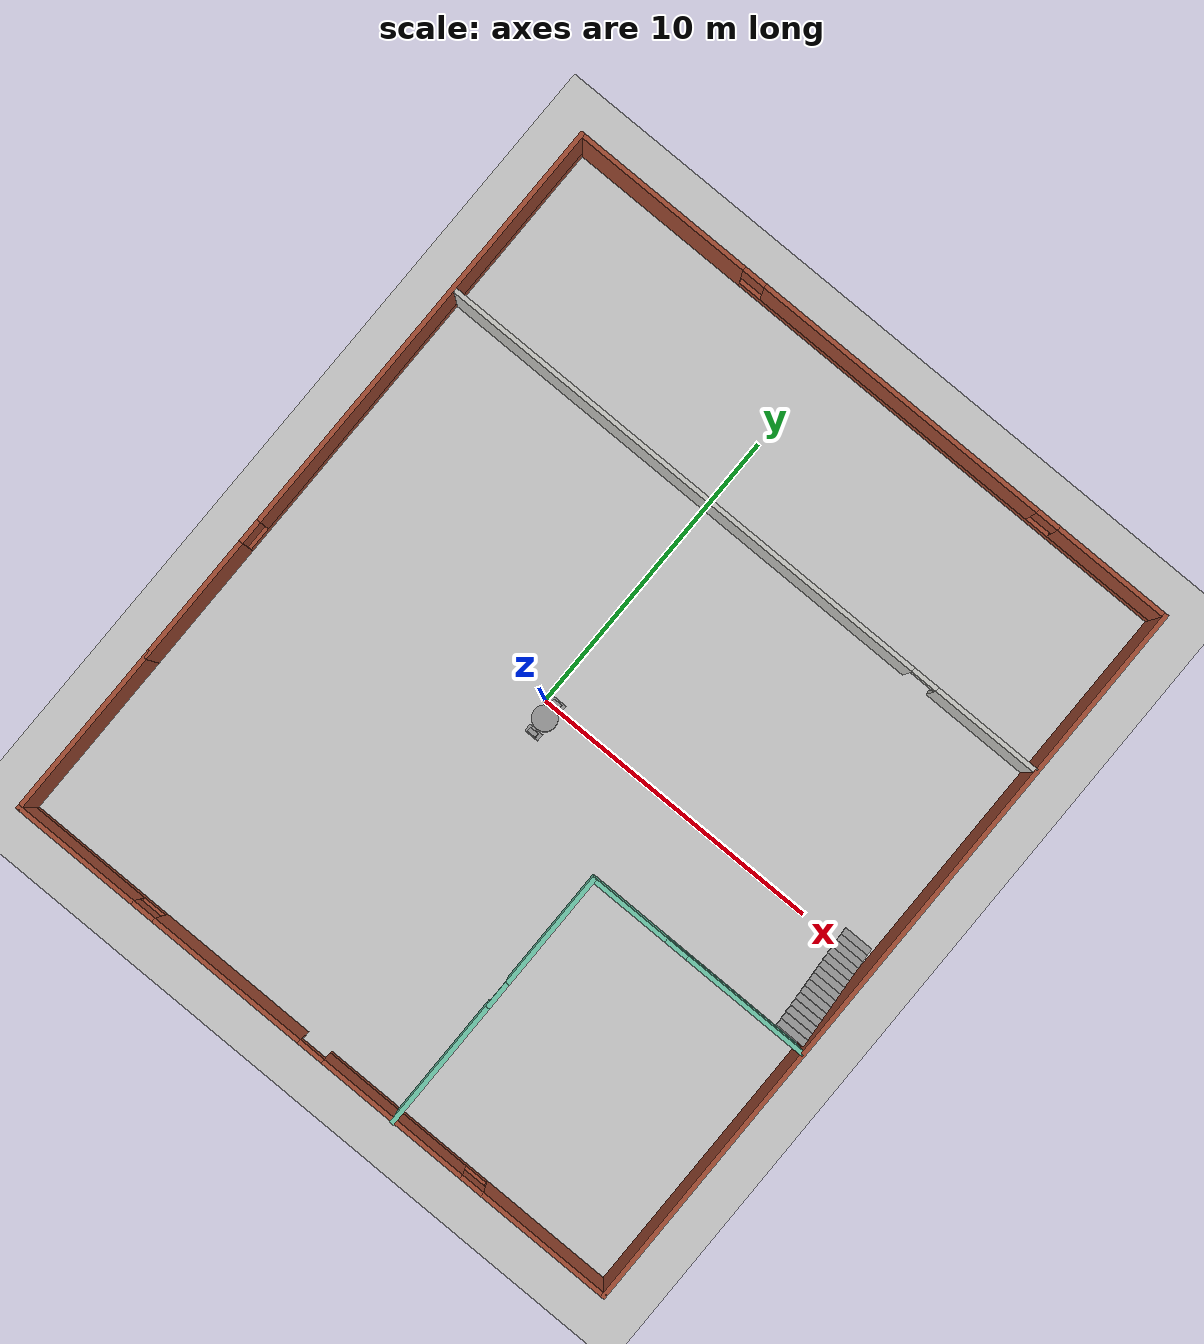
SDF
<sdf version="1.6">
 <world name="default">
  <plugin name="hello" filename="libhello.so"/>
  <light name="sun" type="directional">
   <pose>0 0 10 0 -0 0</pose>
   <diffuse>0.8 0.8 0.8 1</diffuse>
   <specular>0.2 0.2 0.2 1</specular>
   <attenuation>
    <range>1000</range>
    <constant>0.9</constant>
    <linear>0.01</linear>
    <quadratic>0.001</quadratic>
   </attenuation>
   <direction>-0.5 0.1 -0.9</direction>
  </light>
  <model name="ground_plane">
   <static>1</static>
   <link name="link">
    <collision name="collision">
     <geometry><plane><normal>0 0 1</normal><size>100 100</size></plane></geometry>
     <surface>
      <contact><collide_bitmask>65535</collide_bitmask></contact>
      <friction><ode><mu>100</mu><mu2>50</mu2></ode></friction>
     </surface>
    </collision>
    <visual name="visual">
     <cast_shadows>0</cast_shadows>
     <geometry><plane><normal>0 0 1</normal><size>100 100</size></plane></geometry>
     <material>
      <script><uri>file://media/materials/scripts/gazebo.material</uri><name>Gazebo/Grey</name></script>
     </material>
    </visual>
   </link>
  </model>
  <gravity>0 0 -9.8</gravity>
  <magnetic_field>6e-06 2.3e-05 -4.2e-05</magnetic_field>
  <atmosphere type="adiabatic"/>
  <physics name="default_physics" default="0" type="ode">
   <max_step_size>0.001</max_step_size>
   <real_time_factor>1</real_time_factor>
   <real_time_update_rate>1000</real_time_update_rate>
  </physics>
  <scene><ambient>0.4 0.4 0.4 1</ambient><background>0.7 0.7 0.7 1</background><shadows>1</shadows></scene>
  <spherical_coordinates>
   <surface_model>EARTH_WGS84</surface_model>
   <latitude_deg>0</latitude_deg>
   <longitude_deg>0</longitude_deg>
   <elevation>0</elevation>
   <heading_deg>0</heading_deg>
  </spherical_coordinates>
  <model name="robot3">
   <link name="link_2">
    <pose>0.005 -0 -0.064976 0 -0 0</pose>
    <inertial>
     <mass>1</mass>
     <inertia><ixx>0.145833</ixx><ixy>0</ixy><ixz>0</ixz><iyy>0.145833</iyy><iyz>0</iyz><izz>0.125</izz></inertia>
    </inertial>
    <visual name="visual">
     <geometry><cylinder><radius>0.4</radius><length>0.8</length></cylinder></geometry>
     <material>
      <lighting>1</lighting>
      <script><uri>file://media/materials/scripts/gazebo.material</uri><name>Gazebo/Grey</name></script>
      <shader type="pixel"><normal_map>__default__</normal_map></shader>
      <ambient>0.3 0.3 0.3 1</ambient>
      <diffuse>0.7 0.7 0.7 1</diffuse>
      <specular>0.01 0.01 0.01 1</specular>
      <emissive>0 0 0 1</emissive>
     </material>
    </visual>
    <collision name="collision">
     <geometry><cylinder><radius>0.4</radius><length>0.8</length></cylinder></geometry>
     <surface>
      <friction>
       <ode><mu>1</mu><mu2>1</mu2><fdir1>0 0 0</fdir1><slip1>0</slip1><slip2>0</slip2></ode>
       <torsional>
        <coefficient>1</coefficient>
        <patch_radius>0</patch_radius>
        <surface_radius>0</surface_radius>
        <use_patch_radius>1</use_patch_radius>
        <ode><slip>0</slip></ode>
       </torsional>
      </friction>
      <bounce><restitution_coefficient>0</restitution_coefficient><threshold>1e+06</threshold></bounce>
      <contact>
       <collide_without_contact>0</collide_without_contact>
       <collide_without_contact_bitmask>1</collide_without_contact_bitmask>
       <collide_bitmask>1</collide_bitmask>
       <ode>
        <soft_cfm>0</soft_cfm>
        <soft_erp>0.2</soft_erp>
        <kp>1e+13</kp>
        <kd>1</kd>
        <max_vel>0.01</max_vel>
        <min_depth>0</min_depth>
       </ode>
       <bullet>
        <split_impulse>1</split_impulse>
        <split_impulse_penetration_threshold>-0.01</split_impulse_penetration_threshold>
        <soft_cfm>0</soft_cfm>
        <soft_erp>0.2</soft_erp>
        <kp>1e+13</kp>
        <kd>1</kd>
       </bullet>
      </contact>
     </surface>
    </collision>
   </link>
   <link name="link_0">
    <pose>0.00499 0.565134 -0.515032 -0.000625 0 -0.000608</pose>
    <inertial>
     <mass>1</mass>
     <inertia>
      <ixx>0.166667</ixx>
      <ixy>0</ixy>
      <ixz>0</ixz>
      <iyy>0.166667</iyy>
      <iyz>0</iyz>
      <izz>0.166667</izz>
     </inertia>
    </inertial>
    <visual name="visual">
     <geometry><box><size>0.5 0.25 0.1</size></box></geometry>
     <material>
      <lighting>1</lighting>
      <script><uri>file://media/materials/scripts/gazebo.material</uri><name>Gazebo/Grey</name></script>
      <shader type="pixel"><normal_map>__default__</normal_map></shader>
      <ambient>0.3 0.3 0.3 1</ambient>
      <diffuse>0.7 0.7 0.7 1</diffuse>
      <specular>0.01 0.01 0.01 1</specular>
      <emissive>0 0 0 1</emissive>
     </material>
    </visual>
    <collision name="collision">
     <geometry><box><size>0.5 0.25 0.1</size></box></geometry>
     <surface>
      <friction>
       <ode><mu>1</mu><mu2>1</mu2><fdir1>0 0 0</fdir1><slip1>0</slip1><slip2>0</slip2></ode>
       <torsional>
        <coefficient>1</coefficient>
        <patch_radius>0</patch_radius>
        <surface_radius>0</surface_radius>
        <use_patch_radius>1</use_patch_radius>
        <ode><slip>0</slip></ode>
       </torsional>
      </friction>
      <bounce><restitution_coefficient>0</restitution_coefficient><threshold>1e+06</threshold></bounce>
      <contact>
       <collide_without_contact>0</collide_without_contact>
       <collide_without_contact_bitmask>1</collide_without_contact_bitmask>
       <collide_bitmask>1</collide_bitmask>
       <ode>
        <soft_cfm>0</soft_cfm>
        <soft_erp>0.2</soft_erp>
        <kp>1e+13</kp>
        <kd>1</kd>
        <max_vel>0.01</max_vel>
        <min_depth>0</min_depth>
       </ode>
       <bullet>
        <split_impulse>1</split_impulse>
        <split_impulse_penetration_threshold>-0.01</split_impulse_penetration_threshold>
        <soft_cfm>0</soft_cfm>
        <soft_erp>0.2</soft_erp>
        <kp>1e+13</kp>
        <kd>1</kd>
       </bullet>
      </contact>
     </surface>
    </collision>
   </link>
   <link name="link_0_clone">
    <pose>0.00499 -0.535072 -0.514954 -0.00125 -1e-06 -0.001216</pose>
    <inertial>
     <mass>1</mass>
     <inertia>
      <ixx>0.166667</ixx>
      <ixy>0</ixy>
      <ixz>0</ixz>
      <iyy>0.166667</iyy>
      <iyz>0</iyz>
      <izz>0.166667</izz>
     </inertia>
    </inertial>
    <visual name="visual">
     <geometry><box><size>0.5 0.25 0.1</size></box></geometry>
     <material>
      <lighting>1</lighting>
      <script><uri>file://media/materials/scripts/gazebo.material</uri><name>Gazebo/Grey</name></script>
      <shader type="pixel"><normal_map>__default__</normal_map></shader>
      <ambient>0.3 0.3 0.3 1</ambient>
      <diffuse>0.7 0.7 0.7 1</diffuse>
      <specular>0.01 0.01 0.01 1</specular>
      <emissive>0 0 0 1</emissive>
     </material>
    </visual>
    <collision name="collision">
     <geometry><box><size>0.5 0.25 0.1</size></box></geometry>
     <surface>
      <friction>
       <ode><mu>1</mu><mu2>1</mu2><fdir1>0 0 0</fdir1><slip1>0</slip1><slip2>0</slip2></ode>
       <torsional>
        <coefficient>1</coefficient>
        <patch_radius>0</patch_radius>
        <surface_radius>0</surface_radius>
        <use_patch_radius>1</use_patch_radius>
        <ode><slip>0</slip></ode>
       </torsional>
      </friction>
      <bounce><restitution_coefficient>0</restitution_coefficient><threshold>1e+06</threshold></bounce>
      <contact>
       <collide_without_contact>0</collide_without_contact>
       <collide_without_contact_bitmask>1</collide_without_contact_bitmask>
       <collide_bitmask>1</collide_bitmask>
       <ode>
        <soft_cfm>0</soft_cfm>
        <soft_erp>0.2</soft_erp>
        <kp>1e+13</kp>
        <kd>1</kd>
        <max_vel>0.01</max_vel>
        <min_depth>0</min_depth>
       </ode>
       <bullet>
        <split_impulse>1</split_impulse>
        <split_impulse_penetration_threshold>-0.01</split_impulse_penetration_threshold>
        <soft_cfm>0</soft_cfm>
        <soft_erp>0.2</soft_erp>
        <kp>1e+13</kp>
        <kd>1</kd>
       </bullet>
      </contact>
     </surface>
    </collision>
   </link>
   <link name="link_3">
    <pose>-0.015 -1e-06 0.194928 1.5707 -0 0</pose>
    <inertial>
     <mass>1</mass>
     <inertia><ixx>0.145833</ixx><ixy>0</ixy><ixz>0</ixz><iyy>0.145833</iyy><iyz>0</iyz><izz>0.125</izz></inertia>
    </inertial>
    <visual name="visual">
     <geometry><cylinder><radius>0.1</radius><length>1.25</length></cylinder></geometry>
     <material>
      <lighting>1</lighting>
      <script><uri>file://media/materials/scripts/gazebo.material</uri><name>Gazebo/Grey</name></script>
      <shader type="pixel"><normal_map>__default__</normal_map></shader>
      <ambient>0.3 0.3 0.3 1</ambient>
      <diffuse>0.7 0.7 0.7 1</diffuse>
      <specular>0.01 0.01 0.01 1</specular>
      <emissive>0 0 0 1</emissive>
     </material>
    </visual>
    <collision name="collision">
     <geometry><cylinder><radius>0.1</radius><length>1.25</length></cylinder></geometry>
     <surface>
      <friction>
       <ode><mu>1</mu><mu2>1</mu2><fdir1>0 0 0</fdir1><slip1>0</slip1><slip2>0</slip2></ode>
       <torsional>
        <coefficient>1</coefficient>
        <patch_radius>0</patch_radius>
        <surface_radius>0</surface_radius>
        <use_patch_radius>1</use_patch_radius>
        <ode><slip>0</slip></ode>
       </torsional>
      </friction>
      <bounce><restitution_coefficient>0</restitution_coefficient><threshold>1e+06</threshold></bounce>
      <contact>
       <collide_without_contact>0</collide_without_contact>
       <collide_without_contact_bitmask>1</collide_without_contact_bitmask>
       <collide_bitmask>1</collide_bitmask>
       <ode>
        <soft_cfm>0</soft_cfm>
        <soft_erp>0.2</soft_erp>
        <kp>1e+13</kp>
        <kd>1</kd>
        <max_vel>0.01</max_vel>
        <min_depth>0</min_depth>
       </ode>
       <bullet>
        <split_impulse>1</split_impulse>
        <split_impulse_penetration_threshold>-0.01</split_impulse_penetration_threshold>
        <soft_cfm>0</soft_cfm>
        <soft_erp>0.2</soft_erp>
        <kp>1e+13</kp>
        <kd>1</kd>
       </bullet>
      </contact>
     </surface>
    </collision>
   </link>
   <link name="link_4">
    <pose>0.005 -0.550011 -0.064976 0 -0 0</pose>
    <inertial>
     <mass>1</mass>
     <inertia>
      <ixx>0.166667</ixx>
      <ixy>0</ixy>
      <ixz>0</ixz>
      <iyy>0.166667</iyy>
      <iyz>0</iyz>
      <izz>0.166667</izz>
     </inertia>
    </inertial>
    <visual name="visual">
     <geometry><box><size>0.3 0.15 1</size></box></geometry>
     <material>
      <lighting>1</lighting>
      <script><uri>file://media/materials/scripts/gazebo.material</uri><name>Gazebo/Grey</name></script>
      <shader type="pixel"><normal_map>__default__</normal_map></shader>
      <ambient>0.3 0.3 0.3 1</ambient>
      <diffuse>0.7 0.7 0.7 1</diffuse>
      <specular>0.01 0.01 0.01 1</specular>
      <emissive>0 0 0 1</emissive>
     </material>
    </visual>
    <collision name="collision">
     <geometry><box><size>0.3 0.15 1</size></box></geometry>
     <surface>
      <friction>
       <ode><mu>1</mu><mu2>1</mu2><fdir1>0 0 0</fdir1><slip1>0</slip1><slip2>0</slip2></ode>
       <torsional>
        <coefficient>1</coefficient>
        <patch_radius>0</patch_radius>
        <surface_radius>0</surface_radius>
        <use_patch_radius>1</use_patch_radius>
        <ode><slip>0</slip></ode>
       </torsional>
      </friction>
      <bounce><restitution_coefficient>0</restitution_coefficient><threshold>1e+06</threshold></bounce>
      <contact>
       <collide_without_contact>0</collide_without_contact>
       <collide_without_contact_bitmask>1</collide_without_contact_bitmask>
       <collide_bitmask>1</collide_bitmask>
       <ode>
        <soft_cfm>0</soft_cfm>
        <soft_erp>0.2</soft_erp>
        <kp>1e+13</kp>
        <kd>1</kd>
        <max_vel>0.01</max_vel>
        <min_depth>0</min_depth>
       </ode>
       <bullet>
        <split_impulse>1</split_impulse>
        <split_impulse_penetration_threshold>-0.01</split_impulse_penetration_threshold>
        <soft_cfm>0</soft_cfm>
        <soft_erp>0.2</soft_erp>
        <kp>1e+13</kp>
        <kd>1</kd>
       </bullet>
      </contact>
     </surface>
    </collision>
   </link>
   <link name="link_4_clone">
    <pose>0.005 0.550012 -0.064976 0 -0 0</pose>
    <inertial>
     <mass>1</mass>
     <inertia>
      <ixx>0.166667</ixx>
      <ixy>0</ixy>
      <ixz>0</ixz>
      <iyy>0.166667</iyy>
      <iyz>0</iyz>
      <izz>0.166667</izz>
     </inertia>
    </inertial>
    <visual name="visual">
     <geometry><box><size>0.3 0.15 1</size></box></geometry>
     <material>
      <lighting>1</lighting>
      <script><uri>file://media/materials/scripts/gazebo.material</uri><name>Gazebo/Grey</name></script>
      <shader type="pixel"><normal_map>__default__</normal_map></shader>
      <ambient>0.3 0.3 0.3 1</ambient>
      <diffuse>0.7 0.7 0.7 1</diffuse>
      <specular>0.01 0.01 0.01 1</specular>
      <emissive>0 0 0 1</emissive>
     </material>
    </visual>
    <collision name="collision">
     <geometry><box><size>0.3 0.15 1</size></box></geometry>
     <surface>
      <friction>
       <ode><mu>1</mu><mu2>1</mu2><fdir1>0 0 0</fdir1><slip1>0</slip1><slip2>0</slip2></ode>
       <torsional>
        <coefficient>1</coefficient>
        <patch_radius>0</patch_radius>
        <surface_radius>0</surface_radius>
        <use_patch_radius>1</use_patch_radius>
        <ode><slip>0</slip></ode>
       </torsional>
      </friction>
      <bounce><restitution_coefficient>0</restitution_coefficient><threshold>1e+06</threshold></bounce>
      <contact>
       <collide_without_contact>0</collide_without_contact>
       <collide_without_contact_bitmask>1</collide_without_contact_bitmask>
       <collide_bitmask>1</collide_bitmask>
       <ode>
        <soft_cfm>0</soft_cfm>
        <soft_erp>0.2</soft_erp>
        <kp>1e+13</kp>
        <kd>1</kd>
        <max_vel>0.01</max_vel>
        <min_depth>0</min_depth>
       </ode>
       <bullet>
        <split_impulse>1</split_impulse>
        <split_impulse_penetration_threshold>-0.01</split_impulse_penetration_threshold>
        <soft_cfm>0</soft_cfm>
        <soft_erp>0.2</soft_erp>
        <kp>1e+13</kp>
        <kd>1</kd>
       </bullet>
      </contact>
     </surface>
    </collision>
   </link>
   <joint name="link_2_JOINT_2" type="revolute">
    <parent>link_2</parent>
    <child>link_3</child>
    <axis>
     <xyz>1 0 0</xyz>
     <use_parent_model_frame>0</use_parent_model_frame>
     <limit>
      <lower>-1.79769e+308</lower>
      <upper>1.79769e+308</upper>
      <effort>-1</effort>
      <velocity>-1</velocity>
     </limit>
     <dynamics>
      <spring_reference>0</spring_reference>
      <spring_stiffness>0</spring_stiffness>
      <damping>0</damping>
      <friction>0</friction>
     </dynamics>
    </axis>
    <physics>
     <ode><limit><cfm>0</cfm><erp>0.2</erp></limit><suspension><cfm>0</cfm><erp>0.2</erp></suspension></ode>
    </physics>
   </joint>
   <joint name="link_3_JOINT_3" type="revolute">
    <parent>link_3</parent>
    <child>link_4</child>
    <axis>
     <xyz>1 0 0</xyz>
     <use_parent_model_frame>0</use_parent_model_frame>
     <limit>
      <lower>-1.79769e+308</lower>
      <upper>1.79769e+308</upper>
      <effort>-1</effort>
      <velocity>-1</velocity>
     </limit>
     <dynamics>
      <spring_reference>0</spring_reference>
      <spring_stiffness>0</spring_stiffness>
      <damping>0</damping>
      <friction>0</friction>
     </dynamics>
    </axis>
    <physics>
     <ode><limit><cfm>0</cfm><erp>0.2</erp></limit><suspension><cfm>0</cfm><erp>0.2</erp></suspension></ode>
    </physics>
   </joint>
   <joint name="link_3_JOINT_4" type="revolute">
    <parent>link_3</parent>
    <child>link_4_clone</child>
    <axis>
     <xyz>1 0 0</xyz>
     <use_parent_model_frame>0</use_parent_model_frame>
     <limit>
      <lower>-1.79769e+308</lower>
      <upper>1.79769e+308</upper>
      <effort>-1</effort>
      <velocity>-1</velocity>
     </limit>
     <dynamics>
      <spring_reference>0</spring_reference>
      <spring_stiffness>0</spring_stiffness>
      <damping>0</damping>
      <friction>0</friction>
     </dynamics>
    </axis>
    <physics>
     <ode><limit><cfm>0</cfm><erp>0.2</erp></limit><suspension><cfm>0</cfm><erp>0.2</erp></suspension></ode>
    </physics>
   </joint>
   <joint name="link_4_JOINT_1" type="fixed">
    <parent>link_4</parent>
    <child>link_0_clone</child>
    <physics>
     <ode><limit><cfm>0</cfm><erp>0.2</erp></limit><suspension><cfm>0</cfm><erp>0.2</erp></suspension></ode>
    </physics>
   </joint>
   <joint name="link_4_clone_JOINT_0" type="fixed">
    <parent>link_4_clone</parent>
    <child>link_0</child>
    <physics>
     <ode><limit><cfm>0</cfm><erp>0.2</erp></limit><suspension><cfm>0</cfm><erp>0.2</erp></suspension></ode>
    </physics>
   </joint>
   <static>0</static>
   <pose>0.334212 -0.437358 0.565023 -0.000323 -1e-06 0.00236</pose>
  </model>
  <model name="Building">
   <link name="Stairs_0">
    <visual name="Stairs_0_Visual_0">
     <pose>10.3988 -0.214929 0.083333 0 -0 0</pose>
     <geometry><box><size>1 0.233333 0.166667</size></box></geometry>
     <material>
      <script><uri>file://media/materials/scripts/gazebo.material</uri><name>Gazebo/Grey</name></script>
      <ambient>1 1 1 1</ambient>
      <shader type="pixel"/>
      <diffuse>0.7 0.7 0.7 1</diffuse>
      <specular>0.01 0.01 0.01 1</specular>
      <emissive>0 0 0 1</emissive>
     </material>
     <meta><layer>0</layer></meta>
    </visual>
    <visual name="Stairs_0_Visual_1">
     <pose>10.3988 -0.448263 0.25 0 -0 0</pose>
     <geometry><box><size>1 0.233333 0.166667</size></box></geometry>
     <material>
      <script><uri>file://media/materials/scripts/gazebo.material</uri><name>Gazebo/Grey</name></script>
      <ambient>1 1 1 1</ambient>
      <shader type="pixel"/>
      <diffuse>0.7 0.7 0.7 1</diffuse>
      <specular>0.01 0.01 0.01 1</specular>
      <emissive>0 0 0 1</emissive>
     </material>
     <meta><layer>0</layer></meta>
    </visual>
    <visual name="Stairs_0_Visual_2">
     <pose>10.3988 -0.681596 0.416667 0 -0 0</pose>
     <geometry><box><size>1 0.233333 0.166667</size></box></geometry>
     <material>
      <script><uri>file://media/materials/scripts/gazebo.material</uri><name>Gazebo/Grey</name></script>
      <ambient>1 1 1 1</ambient>
      <shader type="pixel"/>
      <diffuse>0.7 0.7 0.7 1</diffuse>
      <specular>0.01 0.01 0.01 1</specular>
      <emissive>0 0 0 1</emissive>
     </material>
     <meta><layer>0</layer></meta>
    </visual>
    <visual name="Stairs_0_Visual_3">
     <pose>10.3988 -0.914929 0.583333 0 -0 0</pose>
     <geometry><box><size>1 0.233333 0.166667</size></box></geometry>
     <material>
      <script><uri>file://media/materials/scripts/gazebo.material</uri><name>Gazebo/Grey</name></script>
      <ambient>1 1 1 1</ambient>
      <shader type="pixel"/>
      <diffuse>0.7 0.7 0.7 1</diffuse>
      <specular>0.01 0.01 0.01 1</specular>
      <emissive>0 0 0 1</emissive>
     </material>
     <meta><layer>0</layer></meta>
    </visual>
    <visual name="Stairs_0_Visual_4">
     <pose>10.3988 -1.14826 0.75 0 -0 0</pose>
     <geometry><box><size>1 0.233333 0.166667</size></box></geometry>
     <material>
      <script><uri>file://media/materials/scripts/gazebo.material</uri><name>Gazebo/Grey</name></script>
      <ambient>1 1 1 1</ambient>
      <shader type="pixel"/>
      <diffuse>0.7 0.7 0.7 1</diffuse>
      <specular>0.01 0.01 0.01 1</specular>
      <emissive>0 0 0 1</emissive>
     </material>
     <meta><layer>0</layer></meta>
    </visual>
    <visual name="Stairs_0_Visual_5">
     <pose>10.3988 -1.3816 0.916667 0 -0 0</pose>
     <geometry><box><size>1 0.233333 0.166667</size></box></geometry>
     <material>
      <script><uri>file://media/materials/scripts/gazebo.material</uri><name>Gazebo/Grey</name></script>
      <ambient>1 1 1 1</ambient>
      <shader type="pixel"/>
      <diffuse>0.7 0.7 0.7 1</diffuse>
      <specular>0.01 0.01 0.01 1</specular>
      <emissive>0 0 0 1</emissive>
     </material>
     <meta><layer>0</layer></meta>
    </visual>
    <visual name="Stairs_0_Visual_6">
     <pose>10.3988 -1.61493 1.08333 0 -0 0</pose>
     <geometry><box><size>1 0.233333 0.166667</size></box></geometry>
     <material>
      <script><uri>file://media/materials/scripts/gazebo.material</uri><name>Gazebo/Grey</name></script>
      <ambient>1 1 1 1</ambient>
      <shader type="pixel"/>
      <diffuse>0.7 0.7 0.7 1</diffuse>
      <specular>0.01 0.01 0.01 1</specular>
      <emissive>0 0 0 1</emissive>
     </material>
     <meta><layer>0</layer></meta>
    </visual>
    <visual name="Stairs_0_Visual_7">
     <pose>10.3988 -1.84826 1.25 0 -0 0</pose>
     <geometry><box><size>1 0.233333 0.166667</size></box></geometry>
     <material>
      <script><uri>file://media/materials/scripts/gazebo.material</uri><name>Gazebo/Grey</name></script>
      <ambient>1 1 1 1</ambient>
      <shader type="pixel"/>
      <diffuse>0.7 0.7 0.7 1</diffuse>
      <specular>0.01 0.01 0.01 1</specular>
      <emissive>0 0 0 1</emissive>
     </material>
     <meta><layer>0</layer></meta>
    </visual>
    <visual name="Stairs_0_Visual_8">
     <pose>10.3988 -2.0816 1.41667 0 -0 0</pose>
     <geometry><box><size>1 0.233333 0.166667</size></box></geometry>
     <material>
      <script><uri>file://media/materials/scripts/gazebo.material</uri><name>Gazebo/Grey</name></script>
      <ambient>1 1 1 1</ambient>
      <shader type="pixel"/>
      <diffuse>0.7 0.7 0.7 1</diffuse>
      <specular>0.01 0.01 0.01 1</specular>
      <emissive>0 0 0 1</emissive>
     </material>
     <meta><layer>0</layer></meta>
    </visual>
    <visual name="Stairs_0_Visual_9">
     <pose>10.3988 -2.31493 1.58333 0 -0 0</pose>
     <geometry><box><size>1 0.233333 0.166667</size></box></geometry>
     <material>
      <script><uri>file://media/materials/scripts/gazebo.material</uri><name>Gazebo/Grey</name></script>
      <ambient>1 1 1 1</ambient>
      <shader type="pixel"/>
      <diffuse>0.7 0.7 0.7 1</diffuse>
      <specular>0.01 0.01 0.01 1</specular>
      <emissive>0 0 0 1</emissive>
     </material>
     <meta><layer>0</layer></meta>
    </visual>
    <visual name="Stairs_0_Visual_10">
     <pose>10.3988 -2.54826 1.75 0 -0 0</pose>
     <geometry><box><size>1 0.233333 0.166667</size></box></geometry>
     <material>
      <script><uri>file://media/materials/scripts/gazebo.material</uri><name>Gazebo/Grey</name></script>
      <ambient>1 1 1 1</ambient>
      <shader type="pixel"/>
      <diffuse>0.7 0.7 0.7 1</diffuse>
      <specular>0.01 0.01 0.01 1</specular>
      <emissive>0 0 0 1</emissive>
     </material>
     <meta><layer>0</layer></meta>
    </visual>
    <visual name="Stairs_0_Visual_11">
     <pose>10.3988 -2.7816 1.91667 0 -0 0</pose>
     <geometry><box><size>1 0.233333 0.166667</size></box></geometry>
     <material>
      <script><uri>file://media/materials/scripts/gazebo.material</uri><name>Gazebo/Grey</name></script>
      <ambient>1 1 1 1</ambient>
      <shader type="pixel"/>
      <diffuse>0.7 0.7 0.7 1</diffuse>
      <specular>0.01 0.01 0.01 1</specular>
      <emissive>0 0 0 1</emissive>
     </material>
     <meta><layer>0</layer></meta>
    </visual>
    <visual name="Stairs_0_Visual_12">
     <pose>10.3988 -3.01493 2.08333 0 -0 0</pose>
     <geometry><box><size>1 0.233333 0.166667</size></box></geometry>
     <material>
      <script><uri>file://media/materials/scripts/gazebo.material</uri><name>Gazebo/Grey</name></script>
      <ambient>1 1 1 1</ambient>
      <shader type="pixel"/>
      <diffuse>0.7 0.7 0.7 1</diffuse>
      <specular>0.01 0.01 0.01 1</specular>
      <emissive>0 0 0 1</emissive>
     </material>
     <meta><layer>0</layer></meta>
    </visual>
    <visual name="Stairs_0_Visual_13">
     <pose>10.3988 -3.24826 2.25 0 -0 0</pose>
     <geometry><box><size>1 0.233333 0.166667</size></box></geometry>
     <material>
      <script><uri>file://media/materials/scripts/gazebo.material</uri><name>Gazebo/Grey</name></script>
      <ambient>1 1 1 1</ambient>
      <shader type="pixel"/>
      <diffuse>0.7 0.7 0.7 1</diffuse>
      <specular>0.01 0.01 0.01 1</specular>
      <emissive>0 0 0 1</emissive>
     </material>
     <meta><layer>0</layer></meta>
    </visual>
    <visual name="Stairs_0_Visual_14">
     <pose>10.3988 -3.4816 2.41667 0 -0 0</pose>
     <geometry><box><size>1 0.233333 0.166667</size></box></geometry>
     <material>
      <script><uri>file://media/materials/scripts/gazebo.material</uri><name>Gazebo/Grey</name></script>
      <ambient>1 1 1 1</ambient>
      <shader type="pixel"/>
      <diffuse>0.7 0.7 0.7 1</diffuse>
      <specular>0.01 0.01 0.01 1</specular>
      <emissive>0 0 0 1</emissive>
     </material>
     <meta><layer>0</layer></meta>
    </visual>
    <collision name="Stairs_0_Collision_0">
     <pose>10.3988 -0.214929 0.083333 0 -0 0</pose>
     <geometry><box><size>1 0.233333 0.166667</size></box></geometry>
     <surface>
      <friction>
       <ode><mu>1</mu><mu2>1</mu2><fdir1>0 0 0</fdir1><slip1>0</slip1><slip2>0</slip2></ode>
       <torsional>
        <coefficient>1</coefficient>
        <patch_radius>0</patch_radius>
        <surface_radius>0</surface_radius>
        <use_patch_radius>1</use_patch_radius>
        <ode><slip>0</slip></ode>
       </torsional>
      </friction>
      <bounce><restitution_coefficient>0</restitution_coefficient><threshold>1e+06</threshold></bounce>
      <contact>
       <collide_without_contact>0</collide_without_contact>
       <collide_without_contact_bitmask>1</collide_without_contact_bitmask>
       <collide_bitmask>1</collide_bitmask>
       <ode>
        <soft_cfm>0</soft_cfm>
        <soft_erp>0.2</soft_erp>
        <kp>1e+13</kp>
        <kd>1</kd>
        <max_vel>0.01</max_vel>
        <min_depth>0</min_depth>
       </ode>
       <bullet>
        <split_impulse>1</split_impulse>
        <split_impulse_penetration_threshold>-0.01</split_impulse_penetration_threshold>
        <soft_cfm>0</soft_cfm>
        <soft_erp>0.2</soft_erp>
        <kp>1e+13</kp>
        <kd>1</kd>
       </bullet>
      </contact>
     </surface>
    </collision>
    <collision name="Stairs_0_Collision_1">
     <pose>10.3988 -0.448263 0.25 0 -0 0</pose>
     <geometry><box><size>1 0.233333 0.166667</size></box></geometry>
     <surface>
      <friction>
       <ode><mu>1</mu><mu2>1</mu2><fdir1>0 0 0</fdir1><slip1>0</slip1><slip2>0</slip2></ode>
       <torsional>
        <coefficient>1</coefficient>
        <patch_radius>0</patch_radius>
        <surface_radius>0</surface_radius>
        <use_patch_radius>1</use_patch_radius>
        <ode><slip>0</slip></ode>
       </torsional>
      </friction>
      <bounce><restitution_coefficient>0</restitution_coefficient><threshold>1e+06</threshold></bounce>
      <contact>
       <collide_without_contact>0</collide_without_contact>
       <collide_without_contact_bitmask>1</collide_without_contact_bitmask>
       <collide_bitmask>1</collide_bitmask>
       <ode>
        <soft_cfm>0</soft_cfm>
        <soft_erp>0.2</soft_erp>
        <kp>1e+13</kp>
        <kd>1</kd>
        <max_vel>0.01</max_vel>
        <min_depth>0</min_depth>
       </ode>
       <bullet>
        <split_impulse>1</split_impulse>
        <split_impulse_penetration_threshold>-0.01</split_impulse_penetration_threshold>
        <soft_cfm>0</soft_cfm>
        <soft_erp>0.2</soft_erp>
        <kp>1e+13</kp>
        <kd>1</kd>
       </bullet>
      </contact>
     </surface>
    </collision>
    <collision name="Stairs_0_Collision_2">
     <pose>10.3988 -0.681596 0.416667 0 -0 0</pose>
     <geometry><box><size>1 0.233333 0.166667</size></box></geometry>
     <surface>
      <friction>
       <ode><mu>1</mu><mu2>1</mu2><fdir1>0 0 0</fdir1><slip1>0</slip1><slip2>0</slip2></ode>
       <torsional>
        <coefficient>1</coefficient>
        <patch_radius>0</patch_radius>
        <surface_radius>0</surface_radius>
        <use_patch_radius>1</use_patch_radius>
        <ode><slip>0</slip></ode>
       </torsional>
      </friction>
      <bounce><restitution_coefficient>0</restitution_coefficient><threshold>1e+06</threshold></bounce>
      <contact>
       <collide_without_contact>0</collide_without_contact>
       <collide_without_contact_bitmask>1</collide_without_contact_bitmask>
       <collide_bitmask>1</collide_bitmask>
       <ode>
        <soft_cfm>0</soft_cfm>
        <soft_erp>0.2</soft_erp>
        <kp>1e+13</kp>
        <kd>1</kd>
        <max_vel>0.01</max_vel>
        <min_depth>0</min_depth>
       </ode>
       <bullet>
        <split_impulse>1</split_impulse>
        <split_impulse_penetration_threshold>-0.01</split_impulse_penetration_threshold>
        <soft_cfm>0</soft_cfm>
        <soft_erp>0.2</soft_erp>
        <kp>1e+13</kp>
        <kd>1</kd>
       </bullet>
      </contact>
     </surface>
    </collision>
    <collision name="Stairs_0_Collision_8">
     <pose>10.3988 -2.0816 1.41667 0 -0 0</pose>
     <geometry><box><size>1 0.233333 0.166667</size></box></geometry>
     <surface>
      <friction>
       <ode><mu>1</mu><mu2>1</mu2><fdir1>0 0 0</fdir1><slip1>0</slip1><slip2>0</slip2></ode>
       <torsional>
        <coefficient>1</coefficient>
        <patch_radius>0</patch_radius>
        <surface_radius>0</surface_radius>
        <use_patch_radius>1</use_patch_radius>
        <ode><slip>0</slip></ode>
       </torsional>
      </friction>
      <bounce><restitution_coefficient>0</restitution_coefficient><threshold>1e+06</threshold></bounce>
      <contact>
       <collide_without_contact>0</collide_without_contact>
       <collide_without_contact_bitmask>1</collide_without_contact_bitmask>
       <collide_bitmask>1</collide_bitmask>
       <ode>
        <soft_cfm>0</soft_cfm>
        <soft_erp>0.2</soft_erp>
        <kp>1e+13</kp>
        <kd>1</kd>
        <max_vel>0.01</max_vel>
        <min_depth>0</min_depth>
       </ode>
       <bullet>
        <split_impulse>1</split_impulse>
        <split_impulse_penetration_threshold>-0.01</split_impulse_penetration_threshold>
        <soft_cfm>0</soft_cfm>
        <soft_erp>0.2</soft_erp>
        <kp>1e+13</kp>
        <kd>1</kd>
       </bullet>
      </contact>
     </surface>
    </collision>
    <collision name="Stairs_0_Collision_3">
     <pose>10.3988 -0.914929 0.583333 0 -0 0</pose>
     <geometry><box><size>1 0.233333 0.166667</size></box></geometry>
     <surface>
      <friction>
       <ode><mu>1</mu><mu2>1</mu2><fdir1>0 0 0</fdir1><slip1>0</slip1><slip2>0</slip2></ode>
       <torsional>
        <coefficient>1</coefficient>
        <patch_radius>0</patch_radius>
        <surface_radius>0</surface_radius>
        <use_patch_radius>1</use_patch_radius>
        <ode><slip>0</slip></ode>
       </torsional>
      </friction>
      <bounce><restitution_coefficient>0</restitution_coefficient><threshold>1e+06</threshold></bounce>
      <contact>
       <collide_without_contact>0</collide_without_contact>
       <collide_without_contact_bitmask>1</collide_without_contact_bitmask>
       <collide_bitmask>1</collide_bitmask>
       <ode>
        <soft_cfm>0</soft_cfm>
        <soft_erp>0.2</soft_erp>
        <kp>1e+13</kp>
        <kd>1</kd>
        <max_vel>0.01</max_vel>
        <min_depth>0</min_depth>
       </ode>
       <bullet>
        <split_impulse>1</split_impulse>
        <split_impulse_penetration_threshold>-0.01</split_impulse_penetration_threshold>
        <soft_cfm>0</soft_cfm>
        <soft_erp>0.2</soft_erp>
        <kp>1e+13</kp>
        <kd>1</kd>
       </bullet>
      </contact>
     </surface>
    </collision>
    <collision name="Stairs_0_Collision_6">
     <pose>10.3988 -1.61493 1.08333 0 -0 0</pose>
     <geometry><box><size>1 0.233333 0.166667</size></box></geometry>
     <surface>
      <friction>
       <ode><mu>1</mu><mu2>1</mu2><fdir1>0 0 0</fdir1><slip1>0</slip1><slip2>0</slip2></ode>
       <torsional>
        <coefficient>1</coefficient>
        <patch_radius>0</patch_radius>
        <surface_radius>0</surface_radius>
        <use_patch_radius>1</use_patch_radius>
        <ode><slip>0</slip></ode>
       </torsional>
      </friction>
      <bounce><restitution_coefficient>0</restitution_coefficient><threshold>1e+06</threshold></bounce>
      <contact>
       <collide_without_contact>0</collide_without_contact>
       <collide_without_contact_bitmask>1</collide_without_contact_bitmask>
       <collide_bitmask>1</collide_bitmask>
       <ode>
        <soft_cfm>0</soft_cfm>
        <soft_erp>0.2</soft_erp>
        <kp>1e+13</kp>
        <kd>1</kd>
        <max_vel>0.01</max_vel>
        <min_depth>0</min_depth>
       </ode>
       <bullet>
        <split_impulse>1</split_impulse>
        <split_impulse_penetration_threshold>-0.01</split_impulse_penetration_threshold>
        <soft_cfm>0</soft_cfm>
        <soft_erp>0.2</soft_erp>
        <kp>1e+13</kp>
        <kd>1</kd>
       </bullet>
      </contact>
     </surface>
    </collision>
    <collision name="Stairs_0_Collision_4">
     <pose>10.3988 -1.14826 0.75 0 -0 0</pose>
     <geometry><box><size>1 0.233333 0.166667</size></box></geometry>
     <surface>
      <friction>
       <ode><mu>1</mu><mu2>1</mu2><fdir1>0 0 0</fdir1><slip1>0</slip1><slip2>0</slip2></ode>
       <torsional>
        <coefficient>1</coefficient>
        <patch_radius>0</patch_radius>
        <surface_radius>0</surface_radius>
        <use_patch_radius>1</use_patch_radius>
        <ode><slip>0</slip></ode>
       </torsional>
      </friction>
      <bounce><restitution_coefficient>0</restitution_coefficient><threshold>1e+06</threshold></bounce>
      <contact>
       <collide_without_contact>0</collide_without_contact>
       <collide_without_contact_bitmask>1</collide_without_contact_bitmask>
       <collide_bitmask>1</collide_bitmask>
       <ode>
        <soft_cfm>0</soft_cfm>
        <soft_erp>0.2</soft_erp>
        <kp>1e+13</kp>
        <kd>1</kd>
        <max_vel>0.01</max_vel>
        <min_depth>0</min_depth>
       </ode>
       <bullet>
        <split_impulse>1</split_impulse>
        <split_impulse_penetration_threshold>-0.01</split_impulse_penetration_threshold>
        <soft_cfm>0</soft_cfm>
        <soft_erp>0.2</soft_erp>
        <kp>1e+13</kp>
        <kd>1</kd>
       </bullet>
      </contact>
     </surface>
    </collision>
    <collision name="Stairs_0_Collision_5">
     <pose>10.3988 -1.3816 0.916667 0 -0 0</pose>
     <geometry><box><size>1 0.233333 0.166667</size></box></geometry>
     <surface>
      <friction>
       <ode><mu>1</mu><mu2>1</mu2><fdir1>0 0 0</fdir1><slip1>0</slip1><slip2>0</slip2></ode>
       <torsional>
        <coefficient>1</coefficient>
        <patch_radius>0</patch_radius>
        <surface_radius>0</surface_radius>
        <use_patch_radius>1</use_patch_radius>
        <ode><slip>0</slip></ode>
       </torsional>
      </friction>
      <bounce><restitution_coefficient>0</restitution_coefficient><threshold>1e+06</threshold></bounce>
      <contact>
       <collide_without_contact>0</collide_without_contact>
       <collide_without_contact_bitmask>1</collide_without_contact_bitmask>
       <collide_bitmask>1</collide_bitmask>
       <ode>
        <soft_cfm>0</soft_cfm>
        <soft_erp>0.2</soft_erp>
        <kp>1e+13</kp>
        <kd>1</kd>
        <max_vel>0.01</max_vel>
        <min_depth>0</min_depth>
       </ode>
       <bullet>
        <split_impulse>1</split_impulse>
        <split_impulse_penetration_threshold>-0.01</split_impulse_penetration_threshold>
        <soft_cfm>0</soft_cfm>
        <soft_erp>0.2</soft_erp>
        <kp>1e+13</kp>
        <kd>1</kd>
       </bullet>
      </contact>
     </surface>
    </collision>
    <collision name="Stairs_0_Collision_7">
     <pose>10.3988 -1.84826 1.25 0 -0 0</pose>
     <geometry><box><size>1 0.233333 0.166667</size></box></geometry>
     <surface>
      <friction>
       <ode><mu>1</mu><mu2>1</mu2><fdir1>0 0 0</fdir1><slip1>0</slip1><slip2>0</slip2></ode>
       <torsional>
        <coefficient>1</coefficient>
        <patch_radius>0</patch_radius>
        <surface_radius>0</surface_radius>
        <use_patch_radius>1</use_patch_radius>
        <ode><slip>0</slip></ode>
       </torsional>
      </friction>
      <bounce><restitution_coefficient>0</restitution_coefficient><threshold>1e+06</threshold></bounce>
      <contact>
       <collide_without_contact>0</collide_without_contact>
       <collide_without_contact_bitmask>1</collide_without_contact_bitmask>
       <collide_bitmask>1</collide_bitmask>
       <ode>
        <soft_cfm>0</soft_cfm>
        <soft_erp>0.2</soft_erp>
        <kp>1e+13</kp>
        <kd>1</kd>
        <max_vel>0.01</max_vel>
        <min_depth>0</min_depth>
       </ode>
       <bullet>
        <split_impulse>1</split_impulse>
        <split_impulse_penetration_threshold>-0.01</split_impulse_penetration_threshold>
        <soft_cfm>0</soft_cfm>
        <soft_erp>0.2</soft_erp>
        <kp>1e+13</kp>
        <kd>1</kd>
       </bullet>
      </contact>
     </surface>
    </collision>
    <collision name="Stairs_0_Collision_9">
     <pose>10.3988 -2.31493 1.58333 0 -0 0</pose>
     <geometry><box><size>1 0.233333 0.166667</size></box></geometry>
     <surface>
      <friction>
       <ode><mu>1</mu><mu2>1</mu2><fdir1>0 0 0</fdir1><slip1>0</slip1><slip2>0</slip2></ode>
       <torsional>
        <coefficient>1</coefficient>
        <patch_radius>0</patch_radius>
        <surface_radius>0</surface_radius>
        <use_patch_radius>1</use_patch_radius>
        <ode><slip>0</slip></ode>
       </torsional>
      </friction>
      <bounce><restitution_coefficient>0</restitution_coefficient><threshold>1e+06</threshold></bounce>
      <contact>
       <collide_without_contact>0</collide_without_contact>
       <collide_without_contact_bitmask>1</collide_without_contact_bitmask>
       <collide_bitmask>1</collide_bitmask>
       <ode>
        <soft_cfm>0</soft_cfm>
        <soft_erp>0.2</soft_erp>
        <kp>1e+13</kp>
        <kd>1</kd>
        <max_vel>0.01</max_vel>
        <min_depth>0</min_depth>
       </ode>
       <bullet>
        <split_impulse>1</split_impulse>
        <split_impulse_penetration_threshold>-0.01</split_impulse_penetration_threshold>
        <soft_cfm>0</soft_cfm>
        <soft_erp>0.2</soft_erp>
        <kp>1e+13</kp>
        <kd>1</kd>
       </bullet>
      </contact>
     </surface>
    </collision>
    <collision name="Stairs_0_Collision_10">
     <pose>10.3988 -2.54826 1.75 0 -0 0</pose>
     <geometry><box><size>1 0.233333 0.166667</size></box></geometry>
     <surface>
      <friction>
       <ode><mu>1</mu><mu2>1</mu2><fdir1>0 0 0</fdir1><slip1>0</slip1><slip2>0</slip2></ode>
       <torsional>
        <coefficient>1</coefficient>
        <patch_radius>0</patch_radius>
        <surface_radius>0</surface_radius>
        <use_patch_radius>1</use_patch_radius>
        <ode><slip>0</slip></ode>
       </torsional>
      </friction>
      <bounce><restitution_coefficient>0</restitution_coefficient><threshold>1e+06</threshold></bounce>
      <contact>
       <collide_without_contact>0</collide_without_contact>
       <collide_without_contact_bitmask>1</collide_without_contact_bitmask>
       <collide_bitmask>1</collide_bitmask>
       <ode>
        <soft_cfm>0</soft_cfm>
        <soft_erp>0.2</soft_erp>
        <kp>1e+13</kp>
        <kd>1</kd>
        <max_vel>0.01</max_vel>
        <min_depth>0</min_depth>
       </ode>
       <bullet>
        <split_impulse>1</split_impulse>
        <split_impulse_penetration_threshold>-0.01</split_impulse_penetration_threshold>
        <soft_cfm>0</soft_cfm>
        <soft_erp>0.2</soft_erp>
        <kp>1e+13</kp>
        <kd>1</kd>
       </bullet>
      </contact>
     </surface>
    </collision>
    <collision name="Stairs_0_Collision_14">
     <pose>10.3988 -3.4816 2.41667 0 -0 0</pose>
     <geometry><box><size>1 0.233333 0.166667</size></box></geometry>
     <surface>
      <friction>
       <ode><mu>1</mu><mu2>1</mu2><fdir1>0 0 0</fdir1><slip1>0</slip1><slip2>0</slip2></ode>
       <torsional>
        <coefficient>1</coefficient>
        <patch_radius>0</patch_radius>
        <surface_radius>0</surface_radius>
        <use_patch_radius>1</use_patch_radius>
        <ode><slip>0</slip></ode>
       </torsional>
      </friction>
      <bounce><restitution_coefficient>0</restitution_coefficient><threshold>1e+06</threshold></bounce>
      <contact>
       <collide_without_contact>0</collide_without_contact>
       <collide_without_contact_bitmask>1</collide_without_contact_bitmask>
       <collide_bitmask>1</collide_bitmask>
       <ode>
        <soft_cfm>0</soft_cfm>
        <soft_erp>0.2</soft_erp>
        <kp>1e+13</kp>
        <kd>1</kd>
        <max_vel>0.01</max_vel>
        <min_depth>0</min_depth>
       </ode>
       <bullet>
        <split_impulse>1</split_impulse>
        <split_impulse_penetration_threshold>-0.01</split_impulse_penetration_threshold>
        <soft_cfm>0</soft_cfm>
        <soft_erp>0.2</soft_erp>
        <kp>1e+13</kp>
        <kd>1</kd>
       </bullet>
      </contact>
     </surface>
    </collision>
    <collision name="Stairs_0_Collision_11">
     <pose>10.3988 -2.7816 1.91667 0 -0 0</pose>
     <geometry><box><size>1 0.233333 0.166667</size></box></geometry>
     <surface>
      <friction>
       <ode><mu>1</mu><mu2>1</mu2><fdir1>0 0 0</fdir1><slip1>0</slip1><slip2>0</slip2></ode>
       <torsional>
        <coefficient>1</coefficient>
        <patch_radius>0</patch_radius>
        <surface_radius>0</surface_radius>
        <use_patch_radius>1</use_patch_radius>
        <ode><slip>0</slip></ode>
       </torsional>
      </friction>
      <bounce><restitution_coefficient>0</restitution_coefficient><threshold>1e+06</threshold></bounce>
      <contact>
       <collide_without_contact>0</collide_without_contact>
       <collide_without_contact_bitmask>1</collide_without_contact_bitmask>
       <collide_bitmask>1</collide_bitmask>
       <ode>
        <soft_cfm>0</soft_cfm>
        <soft_erp>0.2</soft_erp>
        <kp>1e+13</kp>
        <kd>1</kd>
        <max_vel>0.01</max_vel>
        <min_depth>0</min_depth>
       </ode>
       <bullet>
        <split_impulse>1</split_impulse>
        <split_impulse_penetration_threshold>-0.01</split_impulse_penetration_threshold>
        <soft_cfm>0</soft_cfm>
        <soft_erp>0.2</soft_erp>
        <kp>1e+13</kp>
        <kd>1</kd>
       </bullet>
      </contact>
     </surface>
    </collision>
    <collision name="Stairs_0_Collision_12">
     <pose>10.3988 -3.01493 2.08333 0 -0 0</pose>
     <geometry><box><size>1 0.233333 0.166667</size></box></geometry>
     <surface>
      <friction>
       <ode><mu>1</mu><mu2>1</mu2><fdir1>0 0 0</fdir1><slip1>0</slip1><slip2>0</slip2></ode>
       <torsional>
        <coefficient>1</coefficient>
        <patch_radius>0</patch_radius>
        <surface_radius>0</surface_radius>
        <use_patch_radius>1</use_patch_radius>
        <ode><slip>0</slip></ode>
       </torsional>
      </friction>
      <bounce><restitution_coefficient>0</restitution_coefficient><threshold>1e+06</threshold></bounce>
      <contact>
       <collide_without_contact>0</collide_without_contact>
       <collide_without_contact_bitmask>1</collide_without_contact_bitmask>
       <collide_bitmask>1</collide_bitmask>
       <ode>
        <soft_cfm>0</soft_cfm>
        <soft_erp>0.2</soft_erp>
        <kp>1e+13</kp>
        <kd>1</kd>
        <max_vel>0.01</max_vel>
        <min_depth>0</min_depth>
       </ode>
       <bullet>
        <split_impulse>1</split_impulse>
        <split_impulse_penetration_threshold>-0.01</split_impulse_penetration_threshold>
        <soft_cfm>0</soft_cfm>
        <soft_erp>0.2</soft_erp>
        <kp>1e+13</kp>
        <kd>1</kd>
       </bullet>
      </contact>
     </surface>
    </collision>
    <collision name="Stairs_0_Collision_13">
     <pose>10.3988 -3.24826 2.25 0 -0 0</pose>
     <geometry><box><size>1 0.233333 0.166667</size></box></geometry>
     <surface>
      <friction>
       <ode><mu>1</mu><mu2>1</mu2><fdir1>0 0 0</fdir1><slip1>0</slip1><slip2>0</slip2></ode>
       <torsional>
        <coefficient>1</coefficient>
        <patch_radius>0</patch_radius>
        <surface_radius>0</surface_radius>
        <use_patch_radius>1</use_patch_radius>
        <ode><slip>0</slip></ode>
       </torsional>
      </friction>
      <bounce><restitution_coefficient>0</restitution_coefficient><threshold>1e+06</threshold></bounce>
      <contact>
       <collide_without_contact>0</collide_without_contact>
       <collide_without_contact_bitmask>1</collide_without_contact_bitmask>
       <collide_bitmask>1</collide_bitmask>
       <ode>
        <soft_cfm>0</soft_cfm>
        <soft_erp>0.2</soft_erp>
        <kp>1e+13</kp>
        <kd>1</kd>
        <max_vel>0.01</max_vel>
        <min_depth>0</min_depth>
       </ode>
       <bullet>
        <split_impulse>1</split_impulse>
        <split_impulse_penetration_threshold>-0.01</split_impulse_penetration_threshold>
        <soft_cfm>0</soft_cfm>
        <soft_erp>0.2</soft_erp>
        <kp>1e+13</kp>
        <kd>1</kd>
       </bullet>
      </contact>
     </surface>
    </collision>
   </link>
   <link name="Wall_0">
    <pose>-11.05 2.85254 0 0 -0 1.5708</pose>
    <visual name="Wall_0_Visual_0">
     <pose>-7.80775 0 1.25 0 -0 0</pose>
     <geometry><box><size>4.3845 0.15 2.5</size></box></geometry>
     <material>
      <script><uri>file://media/materials/scripts/gazebo.material</uri><name>Gazebo/Bricks</name></script>
      <ambient>1 1 1 1</ambient>
      <shader type="pixel"/>
      <diffuse>1 1 1 1</diffuse>
      <specular>0.2 0.2 0.2 1</specular>
      <emissive>0 0 0 1</emissive>
     </material>
     <meta><layer>0</layer></meta>
    </visual>
    <visual name="Wall_0_Visual_1">
     <pose>2.19225 0 0.25 0 -0 0</pose>
     <geometry><box><size>15.6155 0.15 0.5</size></box></geometry>
     <material>
      <script><uri>file://media/materials/scripts/gazebo.material</uri><name>Gazebo/Bricks</name></script>
      <ambient>1 1 1 1</ambient>
      <shader type="pixel"/>
      <diffuse>1 1 1 1</diffuse>
      <specular>0.2 0.2 0.2 1</specular>
      <emissive>0 0 0 1</emissive>
     </material>
     <meta><layer>0</layer></meta>
    </visual>
    <visual name="Wall_0_Visual_2">
     <pose>2.59225 0 1.5 0 -0 0</pose>
     <geometry><box><size>14.8155 0.15 2</size></box></geometry>
     <material>
      <script><uri>file://media/materials/scripts/gazebo.material</uri><name>Gazebo/Bricks</name></script>
      <ambient>1 1 1 1</ambient>
      <shader type="pixel"/>
      <diffuse>1 1 1 1</diffuse>
      <specular>0.2 0.2 0.2 1</specular>
      <emissive>0 0 0 1</emissive>
     </material>
     <meta><layer>0</layer></meta>
    </visual>
    <visual name="Wall_0_Visual_3">
     <pose>-5.2155 0 1.9 0 -0 0</pose>
     <geometry><box><size>0.8 0.15 1.2</size></box></geometry>
     <material>
      <script><uri>file://media/materials/scripts/gazebo.material</uri><name>Gazebo/Bricks</name></script>
      <ambient>1 1 1 1</ambient>
      <shader type="pixel"/>
      <diffuse>1 1 1 1</diffuse>
      <specular>0.2 0.2 0.2 1</specular>
      <emissive>0 0 0 1</emissive>
     </material>
     <meta><layer>0</layer></meta>
    </visual>
    <collision name="Wall_0_Collision_0">
     <pose>-7.80775 0 1.25 0 -0 0</pose>
     <geometry><box><size>4.3845 0.15 2.5</size></box></geometry>
     <surface>
      <friction>
       <ode><mu>1</mu><mu2>1</mu2><fdir1>0 0 0</fdir1><slip1>0</slip1><slip2>0</slip2></ode>
       <torsional>
        <coefficient>1</coefficient>
        <patch_radius>0</patch_radius>
        <surface_radius>0</surface_radius>
        <use_patch_radius>1</use_patch_radius>
        <ode><slip>0</slip></ode>
       </torsional>
      </friction>
      <bounce><restitution_coefficient>0</restitution_coefficient><threshold>1e+06</threshold></bounce>
      <contact>
       <collide_without_contact>0</collide_without_contact>
       <collide_without_contact_bitmask>1</collide_without_contact_bitmask>
       <collide_bitmask>1</collide_bitmask>
       <ode>
        <soft_cfm>0</soft_cfm>
        <soft_erp>0.2</soft_erp>
        <kp>1e+13</kp>
        <kd>1</kd>
        <max_vel>0.01</max_vel>
        <min_depth>0</min_depth>
       </ode>
       <bullet>
        <split_impulse>1</split_impulse>
        <split_impulse_penetration_threshold>-0.01</split_impulse_penetration_threshold>
        <soft_cfm>0</soft_cfm>
        <soft_erp>0.2</soft_erp>
        <kp>1e+13</kp>
        <kd>1</kd>
       </bullet>
      </contact>
     </surface>
    </collision>
    <collision name="Wall_0_Collision_1">
     <pose>2.19225 0 0.25 0 -0 0</pose>
     <geometry><box><size>15.6155 0.15 0.5</size></box></geometry>
     <surface>
      <friction>
       <ode><mu>1</mu><mu2>1</mu2><fdir1>0 0 0</fdir1><slip1>0</slip1><slip2>0</slip2></ode>
       <torsional>
        <coefficient>1</coefficient>
        <patch_radius>0</patch_radius>
        <surface_radius>0</surface_radius>
        <use_patch_radius>1</use_patch_radius>
        <ode><slip>0</slip></ode>
       </torsional>
      </friction>
      <bounce><restitution_coefficient>0</restitution_coefficient><threshold>1e+06</threshold></bounce>
      <contact>
       <collide_without_contact>0</collide_without_contact>
       <collide_without_contact_bitmask>1</collide_without_contact_bitmask>
       <collide_bitmask>1</collide_bitmask>
       <ode>
        <soft_cfm>0</soft_cfm>
        <soft_erp>0.2</soft_erp>
        <kp>1e+13</kp>
        <kd>1</kd>
        <max_vel>0.01</max_vel>
        <min_depth>0</min_depth>
       </ode>
       <bullet>
        <split_impulse>1</split_impulse>
        <split_impulse_penetration_threshold>-0.01</split_impulse_penetration_threshold>
        <soft_cfm>0</soft_cfm>
        <soft_erp>0.2</soft_erp>
        <kp>1e+13</kp>
        <kd>1</kd>
       </bullet>
      </contact>
     </surface>
    </collision>
    <collision name="Wall_0_Collision_2">
     <pose>2.59225 0 1.5 0 -0 0</pose>
     <geometry><box><size>14.8155 0.15 2</size></box></geometry>
     <surface>
      <friction>
       <ode><mu>1</mu><mu2>1</mu2><fdir1>0 0 0</fdir1><slip1>0</slip1><slip2>0</slip2></ode>
       <torsional>
        <coefficient>1</coefficient>
        <patch_radius>0</patch_radius>
        <surface_radius>0</surface_radius>
        <use_patch_radius>1</use_patch_radius>
        <ode><slip>0</slip></ode>
       </torsional>
      </friction>
      <bounce><restitution_coefficient>0</restitution_coefficient><threshold>1e+06</threshold></bounce>
      <contact>
       <collide_without_contact>0</collide_without_contact>
       <collide_without_contact_bitmask>1</collide_without_contact_bitmask>
       <collide_bitmask>1</collide_bitmask>
       <ode>
        <soft_cfm>0</soft_cfm>
        <soft_erp>0.2</soft_erp>
        <kp>1e+13</kp>
        <kd>1</kd>
        <max_vel>0.01</max_vel>
        <min_depth>0</min_depth>
       </ode>
       <bullet>
        <split_impulse>1</split_impulse>
        <split_impulse_penetration_threshold>-0.01</split_impulse_penetration_threshold>
        <soft_cfm>0</soft_cfm>
        <soft_erp>0.2</soft_erp>
        <kp>1e+13</kp>
        <kd>1</kd>
       </bullet>
      </contact>
     </surface>
    </collision>
    <collision name="Wall_0_Collision_3">
     <pose>-5.2155 0 1.9 0 -0 0</pose>
     <geometry><box><size>0.8 0.15 1.2</size></box></geometry>
     <surface>
      <friction>
       <ode><mu>1</mu><mu2>1</mu2><fdir1>0 0 0</fdir1><slip1>0</slip1><slip2>0</slip2></ode>
       <torsional>
        <coefficient>1</coefficient>
        <patch_radius>0</patch_radius>
        <surface_radius>0</surface_radius>
        <use_patch_radius>1</use_patch_radius>
        <ode><slip>0</slip></ode>
       </torsional>
      </friction>
      <bounce><restitution_coefficient>0</restitution_coefficient><threshold>1e+06</threshold></bounce>
      <contact>
       <collide_without_contact>0</collide_without_contact>
       <collide_without_contact_bitmask>1</collide_without_contact_bitmask>
       <collide_bitmask>1</collide_bitmask>
       <ode>
        <soft_cfm>0</soft_cfm>
        <soft_erp>0.2</soft_erp>
        <kp>1e+13</kp>
        <kd>1</kd>
        <max_vel>0.01</max_vel>
        <min_depth>0</min_depth>
       </ode>
       <bullet>
        <split_impulse>1</split_impulse>
        <split_impulse_penetration_threshold>-0.01</split_impulse_penetration_threshold>
        <soft_cfm>0</soft_cfm>
        <soft_erp>0.2</soft_erp>
        <kp>1e+13</kp>
        <kd>1</kd>
       </bullet>
      </contact>
     </surface>
    </collision>
   </link>
   <link name="Wall_16">
    <pose>3.13852 -8.31175 0 0 -0 1.5708</pose>
    <visual name="Wall_16_Visual_0">
     <pose>-2.44368 0 1.25 0 -0 0</pose>
     <geometry><box><size>4.36265 0.15 2.5</size></box></geometry>
     <material>
      <script><uri>file://media/materials/scripts/gazebo.material</uri><name>Gazebo/Grey</name></script>
      <ambient>0.435294 0.796078 0.67451 1</ambient>
      <shader type="pixel"/>
      <diffuse>0.7 0.7 0.7 1</diffuse>
      <specular>0.01 0.01 0.01 1</specular>
      <emissive>0 0 0 1</emissive>
     </material>
     <meta><layer>0</layer></meta>
    </visual>
    <visual name="Wall_16_Visual_1">
     <pose>2.63132 0 1.25 0 -0 0</pose>
     <geometry><box><size>3.98735 0.15 2.5</size></box></geometry>
     <material>
      <script><uri>file://media/materials/scripts/gazebo.material</uri><name>Gazebo/Grey</name></script>
      <ambient>0.435294 0.796078 0.67451 1</ambient>
      <shader type="pixel"/>
      <diffuse>0.7 0.7 0.7 1</diffuse>
      <specular>0.01 0.01 0.01 1</specular>
      <emissive>0 0 0 1</emissive>
     </material>
     <meta><layer>0</layer></meta>
    </visual>
    <visual name="Wall_16_Visual_2">
     <pose>0.187646 0 2.25 0 -0 0</pose>
     <geometry><box><size>0.9 0.15 0.5</size></box></geometry>
     <material>
      <script><uri>file://media/materials/scripts/gazebo.material</uri><name>Gazebo/Grey</name></script>
      <ambient>0.435294 0.796078 0.67451 1</ambient>
      <shader type="pixel"/>
      <diffuse>0.7 0.7 0.7 1</diffuse>
      <specular>0.01 0.01 0.01 1</specular>
      <emissive>0 0 0 1</emissive>
     </material>
     <meta><layer>0</layer></meta>
    </visual>
    <collision name="Wall_16_Collision_0">
     <pose>-2.44368 0 1.25 0 -0 0</pose>
     <geometry><box><size>4.36265 0.15 2.5</size></box></geometry>
     <surface>
      <friction>
       <ode><mu>1</mu><mu2>1</mu2><fdir1>0 0 0</fdir1><slip1>0</slip1><slip2>0</slip2></ode>
       <torsional>
        <coefficient>1</coefficient>
        <patch_radius>0</patch_radius>
        <surface_radius>0</surface_radius>
        <use_patch_radius>1</use_patch_radius>
        <ode><slip>0</slip></ode>
       </torsional>
      </friction>
      <bounce><restitution_coefficient>0</restitution_coefficient><threshold>1e+06</threshold></bounce>
      <contact>
       <collide_without_contact>0</collide_without_contact>
       <collide_without_contact_bitmask>1</collide_without_contact_bitmask>
       <collide_bitmask>1</collide_bitmask>
       <ode>
        <soft_cfm>0</soft_cfm>
        <soft_erp>0.2</soft_erp>
        <kp>1e+13</kp>
        <kd>1</kd>
        <max_vel>0.01</max_vel>
        <min_depth>0</min_depth>
       </ode>
       <bullet>
        <split_impulse>1</split_impulse>
        <split_impulse_penetration_threshold>-0.01</split_impulse_penetration_threshold>
        <soft_cfm>0</soft_cfm>
        <soft_erp>0.2</soft_erp>
        <kp>1e+13</kp>
        <kd>1</kd>
       </bullet>
      </contact>
     </surface>
    </collision>
    <collision name="Wall_16_Collision_1">
     <pose>2.63132 0 1.25 0 -0 0</pose>
     <geometry><box><size>3.98735 0.15 2.5</size></box></geometry>
     <surface>
      <friction>
       <ode><mu>1</mu><mu2>1</mu2><fdir1>0 0 0</fdir1><slip1>0</slip1><slip2>0</slip2></ode>
       <torsional>
        <coefficient>1</coefficient>
        <patch_radius>0</patch_radius>
        <surface_radius>0</surface_radius>
        <use_patch_radius>1</use_patch_radius>
        <ode><slip>0</slip></ode>
       </torsional>
      </friction>
      <bounce><restitution_coefficient>0</restitution_coefficient><threshold>1e+06</threshold></bounce>
      <contact>
       <collide_without_contact>0</collide_without_contact>
       <collide_without_contact_bitmask>1</collide_without_contact_bitmask>
       <collide_bitmask>1</collide_bitmask>
       <ode>
        <soft_cfm>0</soft_cfm>
        <soft_erp>0.2</soft_erp>
        <kp>1e+13</kp>
        <kd>1</kd>
        <max_vel>0.01</max_vel>
        <min_depth>0</min_depth>
       </ode>
       <bullet>
        <split_impulse>1</split_impulse>
        <split_impulse_penetration_threshold>-0.01</split_impulse_penetration_threshold>
        <soft_cfm>0</soft_cfm>
        <soft_erp>0.2</soft_erp>
        <kp>1e+13</kp>
        <kd>1</kd>
       </bullet>
      </contact>
     </surface>
    </collision>
    <collision name="Wall_16_Collision_2">
     <pose>0.187646 0 2.25 0 -0 0</pose>
     <geometry><box><size>0.9 0.15 0.5</size></box></geometry>
     <surface>
      <friction>
       <ode><mu>1</mu><mu2>1</mu2><fdir1>0 0 0</fdir1><slip1>0</slip1><slip2>0</slip2></ode>
       <torsional>
        <coefficient>1</coefficient>
        <patch_radius>0</patch_radius>
        <surface_radius>0</surface_radius>
        <use_patch_radius>1</use_patch_radius>
        <ode><slip>0</slip></ode>
       </torsional>
      </friction>
      <bounce><restitution_coefficient>0</restitution_coefficient><threshold>1e+06</threshold></bounce>
      <contact>
       <collide_without_contact>0</collide_without_contact>
       <collide_without_contact_bitmask>1</collide_without_contact_bitmask>
       <collide_bitmask>1</collide_bitmask>
       <ode>
        <soft_cfm>0</soft_cfm>
        <soft_erp>0.2</soft_erp>
        <kp>1e+13</kp>
        <kd>1</kd>
        <max_vel>0.01</max_vel>
        <min_depth>0</min_depth>
       </ode>
       <bullet>
        <split_impulse>1</split_impulse>
        <split_impulse_penetration_threshold>-0.01</split_impulse_penetration_threshold>
        <soft_cfm>0</soft_cfm>
        <soft_erp>0.2</soft_erp>
        <kp>1e+13</kp>
        <kd>1</kd>
       </bullet>
      </contact>
     </surface>
    </collision>
   </link>
   <link name="Wall_17">
    <pose>7.06352 -3.76175 0 0 -0 0</pose>
    <visual name="Wall_17_Visual_0">
     <pose>-2.59354 0 1.25 0 -0 0</pose>
     <geometry><box><size>2.81292 0.15 2.5</size></box></geometry>
     <material>
      <script><uri>file://media/materials/scripts/gazebo.material</uri><name>Gazebo/Grey</name></script>
      <ambient>0.435294 0.796078 0.67451 1</ambient>
      <shader type="pixel"/>
      <diffuse>0.7 0.7 0.7 1</diffuse>
      <specular>0.01 0.01 0.01 1</specular>
      <emissive>0 0 0 1</emissive>
     </material>
     <meta><layer>0</layer></meta>
    </visual>
    <visual name="Wall_17_Visual_1">
     <pose>1.40646 0 0.25 0 -0 0</pose>
     <geometry><box><size>5.18708 0.15 0.5</size></box></geometry>
     <material>
      <script><uri>file://media/materials/scripts/gazebo.material</uri><name>Gazebo/Grey</name></script>
      <ambient>0.435294 0.796078 0.67451 1</ambient>
      <shader type="pixel"/>
      <diffuse>0.7 0.7 0.7 1</diffuse>
      <specular>0.01 0.01 0.01 1</specular>
      <emissive>0 0 0 1</emissive>
     </material>
     <meta><layer>0</layer></meta>
    </visual>
    <visual name="Wall_17_Visual_2">
     <pose>1.80646 0 1.5 0 -0 0</pose>
     <geometry><box><size>4.38708 0.15 2</size></box></geometry>
     <material>
      <script><uri>file://media/materials/scripts/gazebo.material</uri><name>Gazebo/Grey</name></script>
      <ambient>0.435294 0.796078 0.67451 1</ambient>
      <shader type="pixel"/>
      <diffuse>0.7 0.7 0.7 1</diffuse>
      <specular>0.01 0.01 0.01 1</specular>
      <emissive>0 0 0 1</emissive>
     </material>
     <meta><layer>0</layer></meta>
    </visual>
    <visual name="Wall_17_Visual_3">
     <pose>-0.787078 0 1.9 0 -0 0</pose>
     <geometry><box><size>0.8 0.15 1.2</size></box></geometry>
     <material>
      <script><uri>file://media/materials/scripts/gazebo.material</uri><name>Gazebo/Grey</name></script>
      <ambient>0.435294 0.796078 0.67451 1</ambient>
      <shader type="pixel"/>
      <diffuse>0.7 0.7 0.7 1</diffuse>
      <specular>0.01 0.01 0.01 1</specular>
      <emissive>0 0 0 1</emissive>
     </material>
     <meta><layer>0</layer></meta>
    </visual>
    <collision name="Wall_17_Collision_0">
     <pose>-2.59354 0 1.25 0 -0 0</pose>
     <geometry><box><size>2.81292 0.15 2.5</size></box></geometry>
     <surface>
      <friction>
       <ode><mu>1</mu><mu2>1</mu2><fdir1>0 0 0</fdir1><slip1>0</slip1><slip2>0</slip2></ode>
       <torsional>
        <coefficient>1</coefficient>
        <patch_radius>0</patch_radius>
        <surface_radius>0</surface_radius>
        <use_patch_radius>1</use_patch_radius>
        <ode><slip>0</slip></ode>
       </torsional>
      </friction>
      <bounce><restitution_coefficient>0</restitution_coefficient><threshold>1e+06</threshold></bounce>
      <contact>
       <collide_without_contact>0</collide_without_contact>
       <collide_without_contact_bitmask>1</collide_without_contact_bitmask>
       <collide_bitmask>1</collide_bitmask>
       <ode>
        <soft_cfm>0</soft_cfm>
        <soft_erp>0.2</soft_erp>
        <kp>1e+13</kp>
        <kd>1</kd>
        <max_vel>0.01</max_vel>
        <min_depth>0</min_depth>
       </ode>
       <bullet>
        <split_impulse>1</split_impulse>
        <split_impulse_penetration_threshold>-0.01</split_impulse_penetration_threshold>
        <soft_cfm>0</soft_cfm>
        <soft_erp>0.2</soft_erp>
        <kp>1e+13</kp>
        <kd>1</kd>
       </bullet>
      </contact>
     </surface>
    </collision>
    <collision name="Wall_17_Collision_1">
     <pose>1.40646 0 0.25 0 -0 0</pose>
     <geometry><box><size>5.18708 0.15 0.5</size></box></geometry>
     <surface>
      <friction>
       <ode><mu>1</mu><mu2>1</mu2><fdir1>0 0 0</fdir1><slip1>0</slip1><slip2>0</slip2></ode>
       <torsional>
        <coefficient>1</coefficient>
        <patch_radius>0</patch_radius>
        <surface_radius>0</surface_radius>
        <use_patch_radius>1</use_patch_radius>
        <ode><slip>0</slip></ode>
       </torsional>
      </friction>
      <bounce><restitution_coefficient>0</restitution_coefficient><threshold>1e+06</threshold></bounce>
      <contact>
       <collide_without_contact>0</collide_without_contact>
       <collide_without_contact_bitmask>1</collide_without_contact_bitmask>
       <collide_bitmask>1</collide_bitmask>
       <ode>
        <soft_cfm>0</soft_cfm>
        <soft_erp>0.2</soft_erp>
        <kp>1e+13</kp>
        <kd>1</kd>
        <max_vel>0.01</max_vel>
        <min_depth>0</min_depth>
       </ode>
       <bullet>
        <split_impulse>1</split_impulse>
        <split_impulse_penetration_threshold>-0.01</split_impulse_penetration_threshold>
        <soft_cfm>0</soft_cfm>
        <soft_erp>0.2</soft_erp>
        <kp>1e+13</kp>
        <kd>1</kd>
       </bullet>
      </contact>
     </surface>
    </collision>
    <collision name="Wall_17_Collision_3">
     <pose>-0.787078 0 1.9 0 -0 0</pose>
     <geometry><box><size>0.8 0.15 1.2</size></box></geometry>
     <surface>
      <friction>
       <ode><mu>1</mu><mu2>1</mu2><fdir1>0 0 0</fdir1><slip1>0</slip1><slip2>0</slip2></ode>
       <torsional>
        <coefficient>1</coefficient>
        <patch_radius>0</patch_radius>
        <surface_radius>0</surface_radius>
        <use_patch_radius>1</use_patch_radius>
        <ode><slip>0</slip></ode>
       </torsional>
      </friction>
      <bounce><restitution_coefficient>0</restitution_coefficient><threshold>1e+06</threshold></bounce>
      <contact>
       <collide_without_contact>0</collide_without_contact>
       <collide_without_contact_bitmask>1</collide_without_contact_bitmask>
       <collide_bitmask>1</collide_bitmask>
       <ode>
        <soft_cfm>0</soft_cfm>
        <soft_erp>0.2</soft_erp>
        <kp>1e+13</kp>
        <kd>1</kd>
        <max_vel>0.01</max_vel>
        <min_depth>0</min_depth>
       </ode>
       <bullet>
        <split_impulse>1</split_impulse>
        <split_impulse_penetration_threshold>-0.01</split_impulse_penetration_threshold>
        <soft_cfm>0</soft_cfm>
        <soft_erp>0.2</soft_erp>
        <kp>1e+13</kp>
        <kd>1</kd>
       </bullet>
      </contact>
     </surface>
    </collision>
    <collision name="Wall_17_Collision_2">
     <pose>1.80646 0 1.5 0 -0 0</pose>
     <geometry><box><size>4.38708 0.15 2</size></box></geometry>
     <surface>
      <friction>
       <ode><mu>1</mu><mu2>1</mu2><fdir1>0 0 0</fdir1><slip1>0</slip1><slip2>0</slip2></ode>
       <torsional>
        <coefficient>1</coefficient>
        <patch_radius>0</patch_radius>
        <surface_radius>0</surface_radius>
        <use_patch_radius>1</use_patch_radius>
        <ode><slip>0</slip></ode>
       </torsional>
      </friction>
      <bounce><restitution_coefficient>0</restitution_coefficient><threshold>1e+06</threshold></bounce>
      <contact>
       <collide_without_contact>0</collide_without_contact>
       <collide_without_contact_bitmask>1</collide_without_contact_bitmask>
       <collide_bitmask>1</collide_bitmask>
       <ode>
        <soft_cfm>0</soft_cfm>
        <soft_erp>0.2</soft_erp>
        <kp>1e+13</kp>
        <kd>1</kd>
        <max_vel>0.01</max_vel>
        <min_depth>0</min_depth>
       </ode>
       <bullet>
        <split_impulse>1</split_impulse>
        <split_impulse_penetration_threshold>-0.01</split_impulse_penetration_threshold>
        <soft_cfm>0</soft_cfm>
        <soft_erp>0.2</soft_erp>
        <kp>1e+13</kp>
        <kd>1</kd>
       </bullet>
      </contact>
     </surface>
    </collision>
   </link>
   <link name="Wall_21">
    <pose>0.035167 6.8887 0 0 -0 0</pose>
    <visual name="Wall_21_Visual_0">
     <pose>-2.31915 0 1.25 0 -0 0</pose>
     <geometry><box><size>17.3617 0.15 2.5</size></box></geometry>
     <material>
      <script><uri>file://media/materials/scripts/gazebo.material</uri><name>Gazebo/CeilingTiled</name></script>
      <ambient>0.996078 0.47451 0.0196078 1</ambient>
      <shader type="pixel"/>
      <diffuse>1 1 1 1</diffuse>
      <specular>0 0 0 1</specular>
      <emissive>0 0 0 1</emissive>
     </material>
     <meta><layer>0</layer></meta>
    </visual>
    <visual name="Wall_21_Visual_1">
     <pose>9.13085 0 1.25 0 -0 0</pose>
     <geometry><box><size>3.7383 0.15 2.5</size></box></geometry>
     <material>
      <script><uri>file://media/materials/scripts/gazebo.material</uri><name>Gazebo/CeilingTiled</name></script>
      <ambient>0.996078 0.47451 0.0196078 1</ambient>
      <shader type="pixel"/>
      <diffuse>1 1 1 1</diffuse>
      <specular>0 0 0 1</specular>
      <emissive>0 0 0 1</emissive>
     </material>
     <meta><layer>0</layer></meta>
    </visual>
    <visual name="Wall_21_Visual_2">
     <pose>6.8117 0 2.25 0 -0 0</pose>
     <geometry><box><size>0.9 0.15 0.5</size></box></geometry>
     <material>
      <script><uri>file://media/materials/scripts/gazebo.material</uri><name>Gazebo/CeilingTiled</name></script>
      <ambient>0.996078 0.47451 0.0196078 1</ambient>
      <shader type="pixel"/>
      <diffuse>1 1 1 1</diffuse>
      <specular>0 0 0 1</specular>
      <emissive>0 0 0 1</emissive>
     </material>
     <meta><layer>0</layer></meta>
    </visual>
    <collision name="Wall_21_Collision_0">
     <pose>-2.31915 0 1.25 0 -0 0</pose>
     <geometry><box><size>17.3617 0.15 2.5</size></box></geometry>
     <surface>
      <friction>
       <ode><mu>1</mu><mu2>1</mu2><fdir1>0 0 0</fdir1><slip1>0</slip1><slip2>0</slip2></ode>
       <torsional>
        <coefficient>1</coefficient>
        <patch_radius>0</patch_radius>
        <surface_radius>0</surface_radius>
        <use_patch_radius>1</use_patch_radius>
        <ode><slip>0</slip></ode>
       </torsional>
      </friction>
      <bounce><restitution_coefficient>0</restitution_coefficient><threshold>1e+06</threshold></bounce>
      <contact>
       <collide_without_contact>0</collide_without_contact>
       <collide_without_contact_bitmask>1</collide_without_contact_bitmask>
       <collide_bitmask>1</collide_bitmask>
       <ode>
        <soft_cfm>0</soft_cfm>
        <soft_erp>0.2</soft_erp>
        <kp>1e+13</kp>
        <kd>1</kd>
        <max_vel>0.01</max_vel>
        <min_depth>0</min_depth>
       </ode>
       <bullet>
        <split_impulse>1</split_impulse>
        <split_impulse_penetration_threshold>-0.01</split_impulse_penetration_threshold>
        <soft_cfm>0</soft_cfm>
        <soft_erp>0.2</soft_erp>
        <kp>1e+13</kp>
        <kd>1</kd>
       </bullet>
      </contact>
     </surface>
    </collision>
    <collision name="Wall_21_Collision_2">
     <pose>6.8117 0 2.25 0 -0 0</pose>
     <geometry><box><size>0.9 0.15 0.5</size></box></geometry>
     <surface>
      <friction>
       <ode><mu>1</mu><mu2>1</mu2><fdir1>0 0 0</fdir1><slip1>0</slip1><slip2>0</slip2></ode>
       <torsional>
        <coefficient>1</coefficient>
        <patch_radius>0</patch_radius>
        <surface_radius>0</surface_radius>
        <use_patch_radius>1</use_patch_radius>
        <ode><slip>0</slip></ode>
       </torsional>
      </friction>
      <bounce><restitution_coefficient>0</restitution_coefficient><threshold>1e+06</threshold></bounce>
      <contact>
       <collide_without_contact>0</collide_without_contact>
       <collide_without_contact_bitmask>1</collide_without_contact_bitmask>
       <collide_bitmask>1</collide_bitmask>
       <ode>
        <soft_cfm>0</soft_cfm>
        <soft_erp>0.2</soft_erp>
        <kp>1e+13</kp>
        <kd>1</kd>
        <max_vel>0.01</max_vel>
        <min_depth>0</min_depth>
       </ode>
       <bullet>
        <split_impulse>1</split_impulse>
        <split_impulse_penetration_threshold>-0.01</split_impulse_penetration_threshold>
        <soft_cfm>0</soft_cfm>
        <soft_erp>0.2</soft_erp>
        <kp>1e+13</kp>
        <kd>1</kd>
       </bullet>
      </contact>
     </surface>
    </collision>
    <collision name="Wall_21_Collision_1">
     <pose>9.13085 0 1.25 0 -0 0</pose>
     <geometry><box><size>3.7383 0.15 2.5</size></box></geometry>
     <surface>
      <friction>
       <ode><mu>1</mu><mu2>1</mu2><fdir1>0 0 0</fdir1><slip1>0</slip1><slip2>0</slip2></ode>
       <torsional>
        <coefficient>1</coefficient>
        <patch_radius>0</patch_radius>
        <surface_radius>0</surface_radius>
        <use_patch_radius>1</use_patch_radius>
        <ode><slip>0</slip></ode>
       </torsional>
      </friction>
      <bounce><restitution_coefficient>0</restitution_coefficient><threshold>1e+06</threshold></bounce>
      <contact>
       <collide_without_contact>0</collide_without_contact>
       <collide_without_contact_bitmask>1</collide_without_contact_bitmask>
       <collide_bitmask>1</collide_bitmask>
       <ode>
        <soft_cfm>0</soft_cfm>
        <soft_erp>0.2</soft_erp>
        <kp>1e+13</kp>
        <kd>1</kd>
        <max_vel>0.01</max_vel>
        <min_depth>0</min_depth>
       </ode>
       <bullet>
        <split_impulse>1</split_impulse>
        <split_impulse_penetration_threshold>-0.01</split_impulse_penetration_threshold>
        <soft_cfm>0</soft_cfm>
        <soft_erp>0.2</soft_erp>
        <kp>1e+13</kp>
        <kd>1</kd>
       </bullet>
      </contact>
     </surface>
    </collision>
   </link>
   <link name="Wall_3">
    <pose>0 12.7775 0 0 -0 0</pose>
    <visual name="Wall_3_Visual_0">
     <pose>-7.99963 0 1.25 0 -0 0</pose>
     <geometry><box><size>6.25074 0.15 2.5</size></box></geometry>
     <material>
      <script><uri>file://media/materials/scripts/gazebo.material</uri><name>Gazebo/Bricks</name></script>
      <ambient>1 1 1 1</ambient>
      <shader type="pixel"/>
      <diffuse>1 1 1 1</diffuse>
      <specular>0.2 0.2 0.2 1</specular>
      <emissive>0 0 0 1</emissive>
     </material>
     <meta><layer>0</layer></meta>
    </visual>
    <visual name="Wall_3_Visual_2">
     <pose>1.08017 0 1.5 0 -0 0</pose>
     <geometry><box><size>10.3089 0.15 2</size></box></geometry>
     <material>
      <script><uri>file://media/materials/scripts/gazebo.material</uri><name>Gazebo/Bricks</name></script>
      <ambient>1 1 1 1</ambient>
      <shader type="pixel"/>
      <diffuse>1 1 1 1</diffuse>
      <specular>0.2 0.2 0.2 1</specular>
      <emissive>0 0 0 1</emissive>
     </material>
     <meta><layer>0</layer></meta>
    </visual>
    <visual name="Wall_3_Visual_1">
     <pose>3.12537 0 0.25 0 -0 0</pose>
     <geometry><box><size>15.9993 0.15 0.5</size></box></geometry>
     <material>
      <script><uri>file://media/materials/scripts/gazebo.material</uri><name>Gazebo/Bricks</name></script>
      <ambient>1 1 1 1</ambient>
      <shader type="pixel"/>
      <diffuse>1 1 1 1</diffuse>
      <specular>0.2 0.2 0.2 1</specular>
      <emissive>0 0 0 1</emissive>
     </material>
     <meta><layer>0</layer></meta>
    </visual>
    <visual name="Wall_3_Visual_3">
     <pose>9.0798 0 1.5 0 -0 0</pose>
     <geometry><box><size>4.0904 0.15 2</size></box></geometry>
     <material>
      <script><uri>file://media/materials/scripts/gazebo.material</uri><name>Gazebo/Bricks</name></script>
      <ambient>1 1 1 1</ambient>
      <shader type="pixel"/>
      <diffuse>1 1 1 1</diffuse>
      <specular>0.2 0.2 0.2 1</specular>
      <emissive>0 0 0 1</emissive>
     </material>
     <meta><layer>0</layer></meta>
    </visual>
    <visual name="Wall_3_Visual_4">
     <pose>-4.47426 0 1.9 0 -0 0</pose>
     <geometry><box><size>0.8 0.15 1.2</size></box></geometry>
     <material>
      <script><uri>file://media/materials/scripts/gazebo.material</uri><name>Gazebo/Bricks</name></script>
      <ambient>1 1 1 1</ambient>
      <shader type="pixel"/>
      <diffuse>1 1 1 1</diffuse>
      <specular>0.2 0.2 0.2 1</specular>
      <emissive>0 0 0 1</emissive>
     </material>
     <meta><layer>0</layer></meta>
    </visual>
    <visual name="Wall_3_Visual_5">
     <pose>6.6346 0 1.9 0 -0 0</pose>
     <geometry><box><size>0.8 0.15 1.2</size></box></geometry>
     <material>
      <script><uri>file://media/materials/scripts/gazebo.material</uri><name>Gazebo/Bricks</name></script>
      <ambient>1 1 1 1</ambient>
      <shader type="pixel"/>
      <diffuse>1 1 1 1</diffuse>
      <specular>0.2 0.2 0.2 1</specular>
      <emissive>0 0 0 1</emissive>
     </material>
     <meta><layer>0</layer></meta>
    </visual>
    <collision name="Wall_3_Collision_0">
     <pose>-7.99963 0 1.25 0 -0 0</pose>
     <geometry><box><size>6.25074 0.15 2.5</size></box></geometry>
     <surface>
      <friction>
       <ode><mu>1</mu><mu2>1</mu2><fdir1>0 0 0</fdir1><slip1>0</slip1><slip2>0</slip2></ode>
       <torsional>
        <coefficient>1</coefficient>
        <patch_radius>0</patch_radius>
        <surface_radius>0</surface_radius>
        <use_patch_radius>1</use_patch_radius>
        <ode><slip>0</slip></ode>
       </torsional>
      </friction>
      <bounce><restitution_coefficient>0</restitution_coefficient><threshold>1e+06</threshold></bounce>
      <contact>
       <collide_without_contact>0</collide_without_contact>
       <collide_without_contact_bitmask>1</collide_without_contact_bitmask>
       <collide_bitmask>1</collide_bitmask>
       <ode>
        <soft_cfm>0</soft_cfm>
        <soft_erp>0.2</soft_erp>
        <kp>1e+13</kp>
        <kd>1</kd>
        <max_vel>0.01</max_vel>
        <min_depth>0</min_depth>
       </ode>
       <bullet>
        <split_impulse>1</split_impulse>
        <split_impulse_penetration_threshold>-0.01</split_impulse_penetration_threshold>
        <soft_cfm>0</soft_cfm>
        <soft_erp>0.2</soft_erp>
        <kp>1e+13</kp>
        <kd>1</kd>
       </bullet>
      </contact>
     </surface>
    </collision>
    <collision name="Wall_3_Collision_1">
     <pose>3.12537 0 0.25 0 -0 0</pose>
     <geometry><box><size>15.9993 0.15 0.5</size></box></geometry>
     <surface>
      <friction>
       <ode><mu>1</mu><mu2>1</mu2><fdir1>0 0 0</fdir1><slip1>0</slip1><slip2>0</slip2></ode>
       <torsional>
        <coefficient>1</coefficient>
        <patch_radius>0</patch_radius>
        <surface_radius>0</surface_radius>
        <use_patch_radius>1</use_patch_radius>
        <ode><slip>0</slip></ode>
       </torsional>
      </friction>
      <bounce><restitution_coefficient>0</restitution_coefficient><threshold>1e+06</threshold></bounce>
      <contact>
       <collide_without_contact>0</collide_without_contact>
       <collide_without_contact_bitmask>1</collide_without_contact_bitmask>
       <collide_bitmask>1</collide_bitmask>
       <ode>
        <soft_cfm>0</soft_cfm>
        <soft_erp>0.2</soft_erp>
        <kp>1e+13</kp>
        <kd>1</kd>
        <max_vel>0.01</max_vel>
        <min_depth>0</min_depth>
       </ode>
       <bullet>
        <split_impulse>1</split_impulse>
        <split_impulse_penetration_threshold>-0.01</split_impulse_penetration_threshold>
        <soft_cfm>0</soft_cfm>
        <soft_erp>0.2</soft_erp>
        <kp>1e+13</kp>
        <kd>1</kd>
       </bullet>
      </contact>
     </surface>
    </collision>
    <collision name="Wall_3_Collision_5">
     <pose>6.6346 0 1.9 0 -0 0</pose>
     <geometry><box><size>0.8 0.15 1.2</size></box></geometry>
     <surface>
      <friction>
       <ode><mu>1</mu><mu2>1</mu2><fdir1>0 0 0</fdir1><slip1>0</slip1><slip2>0</slip2></ode>
       <torsional>
        <coefficient>1</coefficient>
        <patch_radius>0</patch_radius>
        <surface_radius>0</surface_radius>
        <use_patch_radius>1</use_patch_radius>
        <ode><slip>0</slip></ode>
       </torsional>
      </friction>
      <bounce><restitution_coefficient>0</restitution_coefficient><threshold>1e+06</threshold></bounce>
      <contact>
       <collide_without_contact>0</collide_without_contact>
       <collide_without_contact_bitmask>1</collide_without_contact_bitmask>
       <collide_bitmask>1</collide_bitmask>
       <ode>
        <soft_cfm>0</soft_cfm>
        <soft_erp>0.2</soft_erp>
        <kp>1e+13</kp>
        <kd>1</kd>
        <max_vel>0.01</max_vel>
        <min_depth>0</min_depth>
       </ode>
       <bullet>
        <split_impulse>1</split_impulse>
        <split_impulse_penetration_threshold>-0.01</split_impulse_penetration_threshold>
        <soft_cfm>0</soft_cfm>
        <soft_erp>0.2</soft_erp>
        <kp>1e+13</kp>
        <kd>1</kd>
       </bullet>
      </contact>
     </surface>
    </collision>
    <collision name="Wall_3_Collision_2">
     <pose>1.08017 0 1.5 0 -0 0</pose>
     <geometry><box><size>10.3089 0.15 2</size></box></geometry>
     <surface>
      <friction>
       <ode><mu>1</mu><mu2>1</mu2><fdir1>0 0 0</fdir1><slip1>0</slip1><slip2>0</slip2></ode>
       <torsional>
        <coefficient>1</coefficient>
        <patch_radius>0</patch_radius>
        <surface_radius>0</surface_radius>
        <use_patch_radius>1</use_patch_radius>
        <ode><slip>0</slip></ode>
       </torsional>
      </friction>
      <bounce><restitution_coefficient>0</restitution_coefficient><threshold>1e+06</threshold></bounce>
      <contact>
       <collide_without_contact>0</collide_without_contact>
       <collide_without_contact_bitmask>1</collide_without_contact_bitmask>
       <collide_bitmask>1</collide_bitmask>
       <ode>
        <soft_cfm>0</soft_cfm>
        <soft_erp>0.2</soft_erp>
        <kp>1e+13</kp>
        <kd>1</kd>
        <max_vel>0.01</max_vel>
        <min_depth>0</min_depth>
       </ode>
       <bullet>
        <split_impulse>1</split_impulse>
        <split_impulse_penetration_threshold>-0.01</split_impulse_penetration_threshold>
        <soft_cfm>0</soft_cfm>
        <soft_erp>0.2</soft_erp>
        <kp>1e+13</kp>
        <kd>1</kd>
       </bullet>
      </contact>
     </surface>
    </collision>
    <collision name="Wall_3_Collision_3">
     <pose>9.0798 0 1.5 0 -0 0</pose>
     <geometry><box><size>4.0904 0.15 2</size></box></geometry>
     <surface>
      <friction>
       <ode><mu>1</mu><mu2>1</mu2><fdir1>0 0 0</fdir1><slip1>0</slip1><slip2>0</slip2></ode>
       <torsional>
        <coefficient>1</coefficient>
        <patch_radius>0</patch_radius>
        <surface_radius>0</surface_radius>
        <use_patch_radius>1</use_patch_radius>
        <ode><slip>0</slip></ode>
       </torsional>
      </friction>
      <bounce><restitution_coefficient>0</restitution_coefficient><threshold>1e+06</threshold></bounce>
      <contact>
       <collide_without_contact>0</collide_without_contact>
       <collide_without_contact_bitmask>1</collide_without_contact_bitmask>
       <collide_bitmask>1</collide_bitmask>
       <ode>
        <soft_cfm>0</soft_cfm>
        <soft_erp>0.2</soft_erp>
        <kp>1e+13</kp>
        <kd>1</kd>
        <max_vel>0.01</max_vel>
        <min_depth>0</min_depth>
       </ode>
       <bullet>
        <split_impulse>1</split_impulse>
        <split_impulse_penetration_threshold>-0.01</split_impulse_penetration_threshold>
        <soft_cfm>0</soft_cfm>
        <soft_erp>0.2</soft_erp>
        <kp>1e+13</kp>
        <kd>1</kd>
       </bullet>
      </contact>
     </surface>
    </collision>
    <collision name="Wall_3_Collision_4">
     <pose>-4.47426 0 1.9 0 -0 0</pose>
     <geometry><box><size>0.8 0.15 1.2</size></box></geometry>
     <surface>
      <friction>
       <ode><mu>1</mu><mu2>1</mu2><fdir1>0 0 0</fdir1><slip1>0</slip1><slip2>0</slip2></ode>
       <torsional>
        <coefficient>1</coefficient>
        <patch_radius>0</patch_radius>
        <surface_radius>0</surface_radius>
        <use_patch_radius>1</use_patch_radius>
        <ode><slip>0</slip></ode>
       </torsional>
      </friction>
      <bounce><restitution_coefficient>0</restitution_coefficient><threshold>1e+06</threshold></bounce>
      <contact>
       <collide_without_contact>0</collide_without_contact>
       <collide_without_contact_bitmask>1</collide_without_contact_bitmask>
       <collide_bitmask>1</collide_bitmask>
       <ode>
        <soft_cfm>0</soft_cfm>
        <soft_erp>0.2</soft_erp>
        <kp>1e+13</kp>
        <kd>1</kd>
        <max_vel>0.01</max_vel>
        <min_depth>0</min_depth>
       </ode>
       <bullet>
        <split_impulse>1</split_impulse>
        <split_impulse_penetration_threshold>-0.01</split_impulse_penetration_threshold>
        <soft_cfm>0</soft_cfm>
        <soft_erp>0.2</soft_erp>
        <kp>1e+13</kp>
        <kd>1</kd>
       </bullet>
      </contact>
     </surface>
    </collision>
   </link>
   <link name="Wall_4">
    <pose>11.05 -0.022461 0 0 0 -1.5708</pose>
    <visual name="Wall_4_Visual">
     <pose>0 0 1.25 0 -0 0</pose>
     <geometry><box><size>25.75 0.15 2.5</size></box></geometry>
     <material>
      <script><uri>file://media/materials/scripts/gazebo.material</uri><name>Gazebo/Bricks</name></script>
      <ambient>1 1 1 1</ambient>
      <shader type="pixel"/>
      <diffuse>1 1 1 1</diffuse>
      <specular>0.2 0.2 0.2 1</specular>
      <emissive>0 0 0 1</emissive>
     </material>
     <meta><layer>0</layer></meta>
    </visual>
    <collision name="Wall_4_Collision">
     <pose>0 0 1.25 0 -0 0</pose>
     <geometry><box><size>25.75 0.15 2.5</size></box></geometry>
     <surface>
      <friction>
       <ode><mu>1</mu><mu2>1</mu2><fdir1>0 0 0</fdir1><slip1>0</slip1><slip2>0</slip2></ode>
       <torsional>
        <coefficient>1</coefficient>
        <patch_radius>0</patch_radius>
        <surface_radius>0</surface_radius>
        <use_patch_radius>1</use_patch_radius>
        <ode><slip>0</slip></ode>
       </torsional>
      </friction>
      <bounce><restitution_coefficient>0</restitution_coefficient><threshold>1e+06</threshold></bounce>
      <contact>
       <collide_without_contact>0</collide_without_contact>
       <collide_without_contact_bitmask>1</collide_without_contact_bitmask>
       <collide_bitmask>1</collide_bitmask>
       <ode>
        <soft_cfm>0</soft_cfm>
        <soft_erp>0.2</soft_erp>
        <kp>1e+13</kp>
        <kd>1</kd>
        <max_vel>0.01</max_vel>
        <min_depth>0</min_depth>
       </ode>
       <bullet>
        <split_impulse>1</split_impulse>
        <split_impulse_penetration_threshold>-0.01</split_impulse_penetration_threshold>
        <soft_cfm>0</soft_cfm>
        <soft_erp>0.2</soft_erp>
        <kp>1e+13</kp>
        <kd>1</kd>
       </bullet>
      </contact>
     </surface>
    </collision>
   </link>
   <link name="Wall_5">
    <pose>0 -12.8225 0 0 -0 3.14159</pose>
    <visual name="Wall_5_Visual_0">
     <pose>-8.79588 0 1.25 0 -0 0</pose>
     <geometry><box><size>4.65824 0.15 2.5</size></box></geometry>
     <material>
      <script><uri>file://media/materials/scripts/gazebo.material</uri><name>Gazebo/Bricks</name></script>
      <ambient>1 1 1 1</ambient>
      <shader type="pixel"/>
      <diffuse>1 1 1 1</diffuse>
      <specular>0.2 0.2 0.2 1</specular>
      <emissive>0 0 0 1</emissive>
     </material>
     <meta><layer>0</layer></meta>
    </visual>
    <visual name="Wall_5_Visual_2">
     <pose>-3.45759 0 0.25 0 -0 0</pose>
     <geometry><box><size>6.01834 0.15 0.5</size></box></geometry>
     <material>
      <script><uri>file://media/materials/scripts/gazebo.material</uri><name>Gazebo/Bricks</name></script>
      <ambient>1 1 1 1</ambient>
      <shader type="pixel"/>
      <diffuse>1 1 1 1</diffuse>
      <specular>0.2 0.2 0.2 1</specular>
      <emissive>0 0 0 1</emissive>
     </material>
     <meta><layer>0</layer></meta>
    </visual>
    <visual name="Wall_5_Visual_1">
     <pose>3.20234 0 1.25 0 -0 0</pose>
     <geometry><box><size>5.50152 0.15 2.5</size></box></geometry>
     <material>
      <script><uri>file://media/materials/scripts/gazebo.material</uri><name>Gazebo/Bricks</name></script>
      <ambient>1 1 1 1</ambient>
      <shader type="pixel"/>
      <diffuse>1 1 1 1</diffuse>
      <specular>0.2 0.2 0.2 1</specular>
      <emissive>0 0 0 1</emissive>
     </material>
     <meta><layer>0</layer></meta>
    </visual>
    <visual name="Wall_5_Visual_3">
     <pose>8.53905 0 0.25 0 -0 0</pose>
     <geometry><box><size>5.1719 0.15 0.5</size></box></geometry>
     <material>
      <script><uri>file://media/materials/scripts/gazebo.material</uri><name>Gazebo/Bricks</name></script>
      <ambient>1 1 1 1</ambient>
      <shader type="pixel"/>
      <diffuse>1 1 1 1</diffuse>
      <specular>0.2 0.2 0.2 1</specular>
      <emissive>0 0 0 1</emissive>
     </material>
     <meta><layer>0</layer></meta>
    </visual>
    <visual name="Wall_5_Visual_4">
     <pose>-3.05759 0 1.5 0 -0 0</pose>
     <geometry><box><size>5.21834 0.15 2</size></box></geometry>
     <material>
      <script><uri>file://media/materials/scripts/gazebo.material</uri><name>Gazebo/Bricks</name></script>
      <ambient>1 1 1 1</ambient>
      <shader type="pixel"/>
      <diffuse>1 1 1 1</diffuse>
      <specular>0.2 0.2 0.2 1</specular>
      <emissive>0 0 0 1</emissive>
     </material>
     <meta><layer>0</layer></meta>
    </visual>
    <visual name="Wall_5_Visual_5">
     <pose>-3.05759 0 1.5 0 -0 0</pose>
     <geometry><box><size>5.21834 0.15 2</size></box></geometry>
     <material>
      <script><uri>file://media/materials/scripts/gazebo.material</uri><name>Gazebo/Bricks</name></script>
      <ambient>1 1 1 1</ambient>
      <shader type="pixel"/>
      <diffuse>1 1 1 1</diffuse>
      <specular>0.2 0.2 0.2 1</specular>
      <emissive>0 0 0 1</emissive>
     </material>
     <meta><layer>0</layer></meta>
    </visual>
    <visual name="Wall_5_Visual_6">
     <pose>8.93905 0 1.5 0 -0 0</pose>
     <geometry><box><size>4.3719 0.15 2</size></box></geometry>
     <material>
      <script><uri>file://media/materials/scripts/gazebo.material</uri><name>Gazebo/Bricks</name></script>
      <ambient>1 1 1 1</ambient>
      <shader type="pixel"/>
      <diffuse>1 1 1 1</diffuse>
      <specular>0.2 0.2 0.2 1</specular>
      <emissive>0 0 0 1</emissive>
     </material>
     <meta><layer>0</layer></meta>
    </visual>
    <visual name="Wall_5_Visual_7">
     <pose>-6.06676 0 1.9 0 -0 0</pose>
     <geometry><box><size>0.8 0.15 1.2</size></box></geometry>
     <material>
      <script><uri>file://media/materials/scripts/gazebo.material</uri><name>Gazebo/Bricks</name></script>
      <ambient>1 1 1 1</ambient>
      <shader type="pixel"/>
      <diffuse>1 1 1 1</diffuse>
      <specular>0.2 0.2 0.2 1</specular>
      <emissive>0 0 0 1</emissive>
     </material>
     <meta><layer>0</layer></meta>
    </visual>
    <visual name="Wall_5_Visual_8">
     <pose>6.3531 0 1.9 0 -0 0</pose>
     <geometry><box><size>0.8 0.15 1.2</size></box></geometry>
     <material>
      <script><uri>file://media/materials/scripts/gazebo.material</uri><name>Gazebo/Bricks</name></script>
      <ambient>1 1 1 1</ambient>
      <shader type="pixel"/>
      <diffuse>1 1 1 1</diffuse>
      <specular>0.2 0.2 0.2 1</specular>
      <emissive>0 0 0 1</emissive>
     </material>
     <meta><layer>0</layer></meta>
    </visual>
    <visual name="Wall_5_Visual_9">
     <pose>0.001579 0 2.25 0 -0 0</pose>
     <geometry><box><size>0.9 0.15 0.5</size></box></geometry>
     <material>
      <script><uri>file://media/materials/scripts/gazebo.material</uri><name>Gazebo/Bricks</name></script>
      <ambient>1 1 1 1</ambient>
      <shader type="pixel"/>
      <diffuse>1 1 1 1</diffuse>
      <specular>0.2 0.2 0.2 1</specular>
      <emissive>0 0 0 1</emissive>
     </material>
     <meta><layer>0</layer></meta>
    </visual>
    <visual name="Wall_5_Visual_10">
     <pose>0.001579 0 2.25 0 -0 0</pose>
     <geometry><box><size>0.9 0.15 0.5</size></box></geometry>
     <material>
      <script><uri>file://media/materials/scripts/gazebo.material</uri><name>Gazebo/Bricks</name></script>
      <ambient>1 1 1 1</ambient>
      <shader type="pixel"/>
      <diffuse>1 1 1 1</diffuse>
      <specular>0.2 0.2 0.2 1</specular>
      <emissive>0 0 0 1</emissive>
     </material>
     <meta><layer>0</layer></meta>
    </visual>
    <collision name="Wall_5_Collision_0">
     <pose>-8.79588 0 1.25 0 -0 0</pose>
     <geometry><box><size>4.65824 0.15 2.5</size></box></geometry>
     <surface>
      <friction>
       <ode><mu>1</mu><mu2>1</mu2><fdir1>0 0 0</fdir1><slip1>0</slip1><slip2>0</slip2></ode>
       <torsional>
        <coefficient>1</coefficient>
        <patch_radius>0</patch_radius>
        <surface_radius>0</surface_radius>
        <use_patch_radius>1</use_patch_radius>
        <ode><slip>0</slip></ode>
       </torsional>
      </friction>
      <bounce><restitution_coefficient>0</restitution_coefficient><threshold>1e+06</threshold></bounce>
      <contact>
       <collide_without_contact>0</collide_without_contact>
       <collide_without_contact_bitmask>1</collide_without_contact_bitmask>
       <collide_bitmask>1</collide_bitmask>
       <ode>
        <soft_cfm>0</soft_cfm>
        <soft_erp>0.2</soft_erp>
        <kp>1e+13</kp>
        <kd>1</kd>
        <max_vel>0.01</max_vel>
        <min_depth>0</min_depth>
       </ode>
       <bullet>
        <split_impulse>1</split_impulse>
        <split_impulse_penetration_threshold>-0.01</split_impulse_penetration_threshold>
        <soft_cfm>0</soft_cfm>
        <soft_erp>0.2</soft_erp>
        <kp>1e+13</kp>
        <kd>1</kd>
       </bullet>
      </contact>
     </surface>
    </collision>
    <collision name="Wall_5_Collision_3">
     <pose>8.53905 0 0.25 0 -0 0</pose>
     <geometry><box><size>5.1719 0.15 0.5</size></box></geometry>
     <surface>
      <friction>
       <ode><mu>1</mu><mu2>1</mu2><fdir1>0 0 0</fdir1><slip1>0</slip1><slip2>0</slip2></ode>
       <torsional>
        <coefficient>1</coefficient>
        <patch_radius>0</patch_radius>
        <surface_radius>0</surface_radius>
        <use_patch_radius>1</use_patch_radius>
        <ode><slip>0</slip></ode>
       </torsional>
      </friction>
      <bounce><restitution_coefficient>0</restitution_coefficient><threshold>1e+06</threshold></bounce>
      <contact>
       <collide_without_contact>0</collide_without_contact>
       <collide_without_contact_bitmask>1</collide_without_contact_bitmask>
       <collide_bitmask>1</collide_bitmask>
       <ode>
        <soft_cfm>0</soft_cfm>
        <soft_erp>0.2</soft_erp>
        <kp>1e+13</kp>
        <kd>1</kd>
        <max_vel>0.01</max_vel>
        <min_depth>0</min_depth>
       </ode>
       <bullet>
        <split_impulse>1</split_impulse>
        <split_impulse_penetration_threshold>-0.01</split_impulse_penetration_threshold>
        <soft_cfm>0</soft_cfm>
        <soft_erp>0.2</soft_erp>
        <kp>1e+13</kp>
        <kd>1</kd>
       </bullet>
      </contact>
     </surface>
    </collision>
    <collision name="Wall_5_Collision_2">
     <pose>-3.45759 0 0.25 0 -0 0</pose>
     <geometry><box><size>6.01834 0.15 0.5</size></box></geometry>
     <surface>
      <friction>
       <ode><mu>1</mu><mu2>1</mu2><fdir1>0 0 0</fdir1><slip1>0</slip1><slip2>0</slip2></ode>
       <torsional>
        <coefficient>1</coefficient>
        <patch_radius>0</patch_radius>
        <surface_radius>0</surface_radius>
        <use_patch_radius>1</use_patch_radius>
        <ode><slip>0</slip></ode>
       </torsional>
      </friction>
      <bounce><restitution_coefficient>0</restitution_coefficient><threshold>1e+06</threshold></bounce>
      <contact>
       <collide_without_contact>0</collide_without_contact>
       <collide_without_contact_bitmask>1</collide_without_contact_bitmask>
       <collide_bitmask>1</collide_bitmask>
       <ode>
        <soft_cfm>0</soft_cfm>
        <soft_erp>0.2</soft_erp>
        <kp>1e+13</kp>
        <kd>1</kd>
        <max_vel>0.01</max_vel>
        <min_depth>0</min_depth>
       </ode>
       <bullet>
        <split_impulse>1</split_impulse>
        <split_impulse_penetration_threshold>-0.01</split_impulse_penetration_threshold>
        <soft_cfm>0</soft_cfm>
        <soft_erp>0.2</soft_erp>
        <kp>1e+13</kp>
        <kd>1</kd>
       </bullet>
      </contact>
     </surface>
    </collision>
    <collision name="Wall_5_Collision_1">
     <pose>3.20234 0 1.25 0 -0 0</pose>
     <geometry><box><size>5.50152 0.15 2.5</size></box></geometry>
     <surface>
      <friction>
       <ode><mu>1</mu><mu2>1</mu2><fdir1>0 0 0</fdir1><slip1>0</slip1><slip2>0</slip2></ode>
       <torsional>
        <coefficient>1</coefficient>
        <patch_radius>0</patch_radius>
        <surface_radius>0</surface_radius>
        <use_patch_radius>1</use_patch_radius>
        <ode><slip>0</slip></ode>
       </torsional>
      </friction>
      <bounce><restitution_coefficient>0</restitution_coefficient><threshold>1e+06</threshold></bounce>
      <contact>
       <collide_without_contact>0</collide_without_contact>
       <collide_without_contact_bitmask>1</collide_without_contact_bitmask>
       <collide_bitmask>1</collide_bitmask>
       <ode>
        <soft_cfm>0</soft_cfm>
        <soft_erp>0.2</soft_erp>
        <kp>1e+13</kp>
        <kd>1</kd>
        <max_vel>0.01</max_vel>
        <min_depth>0</min_depth>
       </ode>
       <bullet>
        <split_impulse>1</split_impulse>
        <split_impulse_penetration_threshold>-0.01</split_impulse_penetration_threshold>
        <soft_cfm>0</soft_cfm>
        <soft_erp>0.2</soft_erp>
        <kp>1e+13</kp>
        <kd>1</kd>
       </bullet>
      </contact>
     </surface>
    </collision>
    <collision name="Wall_5_Collision_4">
     <pose>-3.05759 0 1.5 0 -0 0</pose>
     <geometry><box><size>5.21834 0.15 2</size></box></geometry>
     <surface>
      <friction>
       <ode><mu>1</mu><mu2>1</mu2><fdir1>0 0 0</fdir1><slip1>0</slip1><slip2>0</slip2></ode>
       <torsional>
        <coefficient>1</coefficient>
        <patch_radius>0</patch_radius>
        <surface_radius>0</surface_radius>
        <use_patch_radius>1</use_patch_radius>
        <ode><slip>0</slip></ode>
       </torsional>
      </friction>
      <bounce><restitution_coefficient>0</restitution_coefficient><threshold>1e+06</threshold></bounce>
      <contact>
       <collide_without_contact>0</collide_without_contact>
       <collide_without_contact_bitmask>1</collide_without_contact_bitmask>
       <collide_bitmask>1</collide_bitmask>
       <ode>
        <soft_cfm>0</soft_cfm>
        <soft_erp>0.2</soft_erp>
        <kp>1e+13</kp>
        <kd>1</kd>
        <max_vel>0.01</max_vel>
        <min_depth>0</min_depth>
       </ode>
       <bullet>
        <split_impulse>1</split_impulse>
        <split_impulse_penetration_threshold>-0.01</split_impulse_penetration_threshold>
        <soft_cfm>0</soft_cfm>
        <soft_erp>0.2</soft_erp>
        <kp>1e+13</kp>
        <kd>1</kd>
       </bullet>
      </contact>
     </surface>
    </collision>
    <collision name="Wall_5_Collision_5">
     <pose>-3.05759 0 1.5 0 -0 0</pose>
     <geometry><box><size>5.21834 0.15 2</size></box></geometry>
     <surface>
      <friction>
       <ode><mu>1</mu><mu2>1</mu2><fdir1>0 0 0</fdir1><slip1>0</slip1><slip2>0</slip2></ode>
       <torsional>
        <coefficient>1</coefficient>
        <patch_radius>0</patch_radius>
        <surface_radius>0</surface_radius>
        <use_patch_radius>1</use_patch_radius>
        <ode><slip>0</slip></ode>
       </torsional>
      </friction>
      <bounce><restitution_coefficient>0</restitution_coefficient><threshold>1e+06</threshold></bounce>
      <contact>
       <collide_without_contact>0</collide_without_contact>
       <collide_without_contact_bitmask>1</collide_without_contact_bitmask>
       <collide_bitmask>1</collide_bitmask>
       <ode>
        <soft_cfm>0</soft_cfm>
        <soft_erp>0.2</soft_erp>
        <kp>1e+13</kp>
        <kd>1</kd>
        <max_vel>0.01</max_vel>
        <min_depth>0</min_depth>
       </ode>
       <bullet>
        <split_impulse>1</split_impulse>
        <split_impulse_penetration_threshold>-0.01</split_impulse_penetration_threshold>
        <soft_cfm>0</soft_cfm>
        <soft_erp>0.2</soft_erp>
        <kp>1e+13</kp>
        <kd>1</kd>
       </bullet>
      </contact>
     </surface>
    </collision>
    <collision name="Wall_5_Collision_7">
     <pose>-6.06676 0 1.9 0 -0 0</pose>
     <geometry><box><size>0.8 0.15 1.2</size></box></geometry>
     <surface>
      <friction>
       <ode><mu>1</mu><mu2>1</mu2><fdir1>0 0 0</fdir1><slip1>0</slip1><slip2>0</slip2></ode>
       <torsional>
        <coefficient>1</coefficient>
        <patch_radius>0</patch_radius>
        <surface_radius>0</surface_radius>
        <use_patch_radius>1</use_patch_radius>
        <ode><slip>0</slip></ode>
       </torsional>
      </friction>
      <bounce><restitution_coefficient>0</restitution_coefficient><threshold>1e+06</threshold></bounce>
      <contact>
       <collide_without_contact>0</collide_without_contact>
       <collide_without_contact_bitmask>1</collide_without_contact_bitmask>
       <collide_bitmask>1</collide_bitmask>
       <ode>
        <soft_cfm>0</soft_cfm>
        <soft_erp>0.2</soft_erp>
        <kp>1e+13</kp>
        <kd>1</kd>
        <max_vel>0.01</max_vel>
        <min_depth>0</min_depth>
       </ode>
       <bullet>
        <split_impulse>1</split_impulse>
        <split_impulse_penetration_threshold>-0.01</split_impulse_penetration_threshold>
        <soft_cfm>0</soft_cfm>
        <soft_erp>0.2</soft_erp>
        <kp>1e+13</kp>
        <kd>1</kd>
       </bullet>
      </contact>
     </surface>
    </collision>
    <collision name="Wall_5_Collision_6">
     <pose>8.93905 0 1.5 0 -0 0</pose>
     <geometry><box><size>4.3719 0.15 2</size></box></geometry>
     <surface>
      <friction>
       <ode><mu>1</mu><mu2>1</mu2><fdir1>0 0 0</fdir1><slip1>0</slip1><slip2>0</slip2></ode>
       <torsional>
        <coefficient>1</coefficient>
        <patch_radius>0</patch_radius>
        <surface_radius>0</surface_radius>
        <use_patch_radius>1</use_patch_radius>
        <ode><slip>0</slip></ode>
       </torsional>
      </friction>
      <bounce><restitution_coefficient>0</restitution_coefficient><threshold>1e+06</threshold></bounce>
      <contact>
       <collide_without_contact>0</collide_without_contact>
       <collide_without_contact_bitmask>1</collide_without_contact_bitmask>
       <collide_bitmask>1</collide_bitmask>
       <ode>
        <soft_cfm>0</soft_cfm>
        <soft_erp>0.2</soft_erp>
        <kp>1e+13</kp>
        <kd>1</kd>
        <max_vel>0.01</max_vel>
        <min_depth>0</min_depth>
       </ode>
       <bullet>
        <split_impulse>1</split_impulse>
        <split_impulse_penetration_threshold>-0.01</split_impulse_penetration_threshold>
        <soft_cfm>0</soft_cfm>
        <soft_erp>0.2</soft_erp>
        <kp>1e+13</kp>
        <kd>1</kd>
       </bullet>
      </contact>
     </surface>
    </collision>
    <collision name="Wall_5_Collision_8">
     <pose>6.3531 0 1.9 0 -0 0</pose>
     <geometry><box><size>0.8 0.15 1.2</size></box></geometry>
     <surface>
      <friction>
       <ode><mu>1</mu><mu2>1</mu2><fdir1>0 0 0</fdir1><slip1>0</slip1><slip2>0</slip2></ode>
       <torsional>
        <coefficient>1</coefficient>
        <patch_radius>0</patch_radius>
        <surface_radius>0</surface_radius>
        <use_patch_radius>1</use_patch_radius>
        <ode><slip>0</slip></ode>
       </torsional>
      </friction>
      <bounce><restitution_coefficient>0</restitution_coefficient><threshold>1e+06</threshold></bounce>
      <contact>
       <collide_without_contact>0</collide_without_contact>
       <collide_without_contact_bitmask>1</collide_without_contact_bitmask>
       <collide_bitmask>1</collide_bitmask>
       <ode>
        <soft_cfm>0</soft_cfm>
        <soft_erp>0.2</soft_erp>
        <kp>1e+13</kp>
        <kd>1</kd>
        <max_vel>0.01</max_vel>
        <min_depth>0</min_depth>
       </ode>
       <bullet>
        <split_impulse>1</split_impulse>
        <split_impulse_penetration_threshold>-0.01</split_impulse_penetration_threshold>
        <soft_cfm>0</soft_cfm>
        <soft_erp>0.2</soft_erp>
        <kp>1e+13</kp>
        <kd>1</kd>
       </bullet>
      </contact>
     </surface>
    </collision>
    <collision name="Wall_5_Collision_9">
     <pose>0.001579 0 2.25 0 -0 0</pose>
     <geometry><box><size>0.9 0.15 0.5</size></box></geometry>
     <surface>
      <friction>
       <ode><mu>1</mu><mu2>1</mu2><fdir1>0 0 0</fdir1><slip1>0</slip1><slip2>0</slip2></ode>
       <torsional>
        <coefficient>1</coefficient>
        <patch_radius>0</patch_radius>
        <surface_radius>0</surface_radius>
        <use_patch_radius>1</use_patch_radius>
        <ode><slip>0</slip></ode>
       </torsional>
      </friction>
      <bounce><restitution_coefficient>0</restitution_coefficient><threshold>1e+06</threshold></bounce>
      <contact>
       <collide_without_contact>0</collide_without_contact>
       <collide_without_contact_bitmask>1</collide_without_contact_bitmask>
       <collide_bitmask>1</collide_bitmask>
       <ode>
        <soft_cfm>0</soft_cfm>
        <soft_erp>0.2</soft_erp>
        <kp>1e+13</kp>
        <kd>1</kd>
        <max_vel>0.01</max_vel>
        <min_depth>0</min_depth>
       </ode>
       <bullet>
        <split_impulse>1</split_impulse>
        <split_impulse_penetration_threshold>-0.01</split_impulse_penetration_threshold>
        <soft_cfm>0</soft_cfm>
        <soft_erp>0.2</soft_erp>
        <kp>1e+13</kp>
        <kd>1</kd>
       </bullet>
      </contact>
     </surface>
    </collision>
    <collision name="Wall_5_Collision_10">
     <pose>0.001579 0 2.25 0 -0 0</pose>
     <geometry><box><size>0.9 0.15 0.5</size></box></geometry>
     <surface>
      <friction>
       <ode><mu>1</mu><mu2>1</mu2><fdir1>0 0 0</fdir1><slip1>0</slip1><slip2>0</slip2></ode>
       <torsional>
        <coefficient>1</coefficient>
        <patch_radius>0</patch_radius>
        <surface_radius>0</surface_radius>
        <use_patch_radius>1</use_patch_radius>
        <ode><slip>0</slip></ode>
       </torsional>
      </friction>
      <bounce><restitution_coefficient>0</restitution_coefficient><threshold>1e+06</threshold></bounce>
      <contact>
       <collide_without_contact>0</collide_without_contact>
       <collide_without_contact_bitmask>1</collide_without_contact_bitmask>
       <collide_bitmask>1</collide_bitmask>
       <ode>
        <soft_cfm>0</soft_cfm>
        <soft_erp>0.2</soft_erp>
        <kp>1e+13</kp>
        <kd>1</kd>
        <max_vel>0.01</max_vel>
        <min_depth>0</min_depth>
       </ode>
       <bullet>
        <split_impulse>1</split_impulse>
        <split_impulse_penetration_threshold>-0.01</split_impulse_penetration_threshold>
        <soft_cfm>0</soft_cfm>
        <soft_erp>0.2</soft_erp>
        <kp>1e+13</kp>
        <kd>1</kd>
       </bullet>
      </contact>
     </surface>
    </collision>
   </link>
   <link name="Wall_6">
    <pose>-11.05 -9.89746 0 0 -0 1.5708</pose>
    <visual name="Wall_6_Visual">
     <pose>0 0 1.25 0 -0 0</pose>
     <geometry><box><size>6 0.15 2.5</size></box></geometry>
     <material>
      <script><uri>file://media/materials/scripts/gazebo.material</uri><name>Gazebo/Bricks</name></script>
      <ambient>1 1 1 1</ambient>
      <shader type="pixel"/>
      <diffuse>1 1 1 1</diffuse>
      <specular>0.2 0.2 0.2 1</specular>
      <emissive>0 0 0 1</emissive>
     </material>
     <meta><layer>0</layer></meta>
    </visual>
    <collision name="Wall_6_Collision">
     <pose>0 0 1.25 0 -0 0</pose>
     <geometry><box><size>6 0.15 2.5</size></box></geometry>
     <surface>
      <friction>
       <ode><mu>1</mu><mu2>1</mu2><fdir1>0 0 0</fdir1><slip1>0</slip1><slip2>0</slip2></ode>
       <torsional>
        <coefficient>1</coefficient>
        <patch_radius>0</patch_radius>
        <surface_radius>0</surface_radius>
        <use_patch_radius>1</use_patch_radius>
        <ode><slip>0</slip></ode>
       </torsional>
      </friction>
      <bounce><restitution_coefficient>0</restitution_coefficient><threshold>1e+06</threshold></bounce>
      <contact>
       <collide_without_contact>0</collide_without_contact>
       <collide_without_contact_bitmask>1</collide_without_contact_bitmask>
       <collide_bitmask>1</collide_bitmask>
       <ode>
        <soft_cfm>0</soft_cfm>
        <soft_erp>0.2</soft_erp>
        <kp>1e+13</kp>
        <kd>1</kd>
        <max_vel>0.01</max_vel>
        <min_depth>0</min_depth>
       </ode>
       <bullet>
        <split_impulse>1</split_impulse>
        <split_impulse_penetration_threshold>-0.01</split_impulse_penetration_threshold>
        <soft_cfm>0</soft_cfm>
        <soft_erp>0.2</soft_erp>
        <kp>1e+13</kp>
        <kd>1</kd>
       </bullet>
      </contact>
     </surface>
    </collision>
   </link>
   <static>1</static>
   <pose>1.3463 0.605074 0 0 -0 0</pose>
  </model>
 </world>
</sdf>
